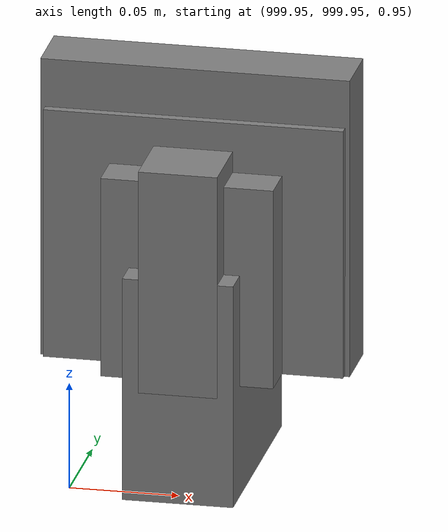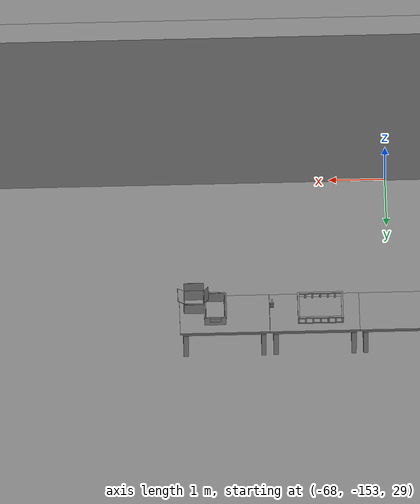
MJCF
<mujoco>
    <option gravity="0.000000000 0.000000000 -9.810000420" timestep="0.0049999999" integrator="implicitfast" density="1.225" viscosity="1.8000001e-05" noslip_iterations="10" iterations="100" sdf_iterations="50">
        <flag multiccd="disable"/>
    </option>
    <size memory="1000M"/>
    <compiler coordinate="local"/>
    <worldbody>
        <light cutoff="30" pos="0 1 1" dir="0 -1 -2"/>
        <light cutoff="30" pos="0 -1 1" dir="0 1 -2"/>
        <body pos="1000.000000000 1000.000000000 1.000000000" euler="0.000011953 0.000005123 -179.999984741" name="openloong_gripper_2f85_fix_base_usda_intel_box">
            <geom contype="1" conaffinity="1" density="1000" type="box" material="" rgba="0.500000000 0.500000000 0.500000000 1.000000000" solimp="0.899999976 0.949999988 0.001000000" friction="1.000000000 0.005000000 0.000100000" solref="0.020000000 1.000000000" margin="0" condim="3" group="0" pos="0.000000000 -0.000067139 0.000082284" quat="0.707106709 0.000000225 0.000000253 0.707106650" size="0.052800003 0.025300000 0.052800003" name="openloong_gripper_2f85_fix_base_usda_geom_FCBDBEA7_FFE3_49C6_9F52_89108464222C"/>
            <freejoint name="openloong_gripper_2f85_fix_base_usda_intel_box_joint"/>
            <site size="0.005000000 0.005000000 0.005000000" rgba="0.500000000 0.500000000 0.500000000 1.000000000" pos="0.000000000 0.000000000 0.000000000" quat="0.999961913 0.008726500 0.000000000 0.000000000" group="0" type="sphere" name="openloong_gripper_2f85_fix_base_usda_intel_boxsite"/>
        </body>
        <body pos="1000.000000000 999.999938965 1.000000000" euler="0.000000000 0.000000000 180.000000000" name="openloong_gripper_2f85_fix_base_usda_intelcore_i5">
            <geom contype="1" conaffinity="1" density="1000" type="box" material="" rgba="0.500000000 0.500000000 0.500000000 1.000000000" solimp="0.899999976 0.949999988 0.001000000" friction="1.000000000 0.005000000 0.000100000" solref="0.020000000 1.000000000" margin="0" condim="3" group="0" pos="0.000000000 0.000000000 0.051722717" quat="0.707106709 0.000000000 0.000000000 -0.707106769" size="0.052800000 0.018080002 0.052800000" name="openloong_gripper_2f85_fix_base_usda_geom_BCCCB434_B437_4029_AC8D_9703CF9488B4"/>
            <freejoint name="openloong_gripper_2f85_fix_base_usda_intelcore_i5_joint"/>
            <site size="0.005000000 0.005000000 0.005000000" rgba="0.500000000 0.500000000 0.500000000 1.000000000" pos="0.000000000 0.000000000 0.000000000" quat="0.999961913 0.008726534 0.000000000 0.000000000" group="0" type="sphere" name="openloong_gripper_2f85_fix_base_usda_intelcore_i5site"/>
        </body>
        <body pos="-66.005027771 -149.768493652 31.171264648" euler="160.226028442 -70.343513489 -176.699813843" mocap="true" name="spotlight5_SpotLight"/>
        <body pos="-66.360572815 -149.628311157 31.167764664" euler="-173.206497192 82.990631104 -173.107055664" mocap="true" name="spotlight6_SpotLight"/>
        <body pos="1000.000000000 1000.000000000 1.000000000" euler="0.000000000 0.000000000 180.000000000" name="openloong_gripper_2f85_fix_base_usda_wifi_box">
            <geom contype="1" conaffinity="1" density="1000" type="box" material="" rgba="0.500000000 0.500000000 0.500000000 1.000000000" solimp="0.899999976 0.949999988 0.001000000" friction="1.000000000 0.005000000 0.000100000" solref="0.020000000 1.000000000" margin="0" condim="3" group="0" pos="0.000000000 0.000000000 0.058978677" quat="0.000000000 0.000000047 0.000000000 1.000000000" size="0.068499997 0.018999999 0.059000000" name="openloong_gripper_2f85_fix_base_usda_geom_CA61DD2F_25D5_45C3_B92F_5000E40BD1D1"/>
            <freejoint name="openloong_gripper_2f85_fix_base_usda_wifi_box_joint"/>
            <site size="0.005000000 0.005000000 0.005000000" rgba="0.500000000 0.500000000 0.500000000 1.000000000" pos="0.000000000 0.000000000 0.000000000" quat="0.999961913 0.008726500 0.000000000 0.000000000" group="0" type="sphere" name="openloong_gripper_2f85_fix_base_usda_wifi_boxsite"/>
        </body>
        <body pos="1000.000000000 1000.000000000 1.000000000" euler="0.000000000 0.000000000 180.000000000" name="openloong_gripper_2f85_fix_base_usda_cpu_fan">
            <geom contype="1" conaffinity="1" density="1000" type="box" material="" rgba="0.500000000 0.500000000 0.500000000 1.000000000" solimp="0.899999976 0.949999988 0.001000000" friction="1.000000000 0.005000000 0.000100000" solref="0.020000000 1.000000000" margin="0" condim="3" group="0" pos="0.000000000 0.000000000 0.070034981" quat="0.000000000 0.000000000 0.000000000 1.000000000" size="0.070700005 0.014699999 0.070700005" name="openloong_gripper_2f85_fix_base_usda_geom_E3F388F2_4A1F_4000_9D7A_EF58941BE844"/>
            <freejoint name="openloong_gripper_2f85_fix_base_usda_cpu_fan_joint"/>
            <site size="0.005000000 0.005000000 0.005000000" rgba="0.500000000 0.500000000 0.500000000 1.000000000" pos="0.000000000 0.000000000 0.000000000" quat="0.999961913 0.008726535 0.000000000 0.000000000" group="0" type="sphere" name="openloong_gripper_2f85_fix_base_usda_cpu_fancsite"/>
        </body>
        <body pos="-65.888198853 -149.799346924 31.171499252" euler="-107.740707397 -33.283966064 76.697357178" mocap="true" name="spotlight3_SpotLight"/>
        <body pos="1000.000000000 1000.000000000 1.000000000" euler="0.000000000 0.000000000 180.000000000" name="openloong_gripper_2f85_fix_base_usda_battery_01">
            <geom contype="1" conaffinity="1" density="1000" type="box" material="" rgba="0.500000000 0.500000000 0.500000000 1.000000000" solimp="0.899999976 0.949999988 0.001000000" friction="1.000000000 0.005000000 0.000100000" solref="0.020000000 1.000000000" margin="0" condim="3" group="0" pos="-0.011123657 -0.041940309 0.101691343" quat="1.000000000 0.000000000 0.000000000 0.000000000" size="0.010800000 0.003375000 0.004725000" name="openloong_gripper_2f85_fix_base_usda_geom_D9E7F78D_7C33_432E_8BDD_4C954EC26A77"/>
            <geom contype="1" conaffinity="1" density="1000" type="box" material="" rgba="0.500000000 0.500000000 0.500000000 1.000000000" solimp="0.899999976 0.949999988 0.001000000" friction="1.000000000 0.005000000 0.000100000" solref="0.020000000 1.000000000" margin="0" condim="3" group="0" pos="-0.010876465 -0.044247437 0.047066893" quat="0.998702705 -0.050920475 0.000000000 0.000000000" size="0.009450001 0.002700000 0.024975000" name="openloong_gripper_2f85_fix_base_usda_geom_8815689E_2B96_46C6_894E_3B05D87EB9F1"/>
            <geom contype="1" conaffinity="1" density="1000" type="box" material="" rgba="0.500000000 0.500000000 0.500000000 1.000000000" solimp="0.899999976 0.949999988 0.001000000" friction="1.000000000 0.005000000 0.000100000" solref="0.020000000 1.000000000" margin="0" condim="3" group="0" pos="-0.001235962 -0.000659180 0.047381196" quat="1.000000000 0.000000000 0.000000000 0.000000000" size="0.039420001 0.039150000 0.047250003" name="openloong_gripper_2f85_fix_base_usda_geom_19D9F129_815C_4E70_A973_94E51340F044"/>
            <geom contype="1" conaffinity="1" density="1000" type="box" material="" rgba="0.500000000 0.500000000 0.500000000 1.000000000" solimp="0.899999976 0.949999988 0.001000000" friction="1.000000000 0.005000000 0.000100000" solref="0.020000000 1.000000000" margin="0" condim="3" group="0" pos="-0.010876465 -0.039138794 0.009851727" quat="1.000000000 0.000000000 0.000000000 0.000000000" size="0.009450001 0.010800000 0.013500000" name="openloong_gripper_2f85_fix_base_usda_geom_5CC1B9B1_C5BD_4FF8_B424_7BB6FA3D0E09"/>
            <geom contype="1" conaffinity="1" density="1000" type="box" material="" rgba="0.500000000 0.500000000 0.500000000 1.000000000" solimp="0.899999976 0.949999988 0.001000000" friction="1.000000000 0.005000000 0.000100000" solref="0.020000000 1.000000000" margin="0" condim="3" group="0" pos="-0.010876465 -0.041528322 0.071508206" quat="1.000000000 0.000000000 0.000000000 0.000000000" size="0.009450001 0.002700000 0.027000001" name="openloong_gripper_2f85_fix_base_usda_geom_3039782F_AFCE_42D6_BDC4_063E17A888EF"/>
            <freejoint name="openloong_gripper_2f85_fix_base_usda_battery_01_joint"/>
            <site size="0.005000000 0.005000000 0.005000000" rgba="0.500000000 0.500000000 0.500000000 1.000000000" pos="0.000000000 0.000000000 0.000000000" quat="0.999961913 0.008726500 0.000000000 0.000000000" group="0" type="sphere" name="openloong_gripper_2f85_fix_base_usda_battery_01site"/>
        </body>
        <body pos="-64.866622925 -149.383972168 30.183746338" euler="89.999984741 89.999946594 0.000000000" name="openloong_gripper_2f85_fix_base_usda_bluebox_01">
            <geom contype="1" conaffinity="1" density="1000" type="box" material="" rgba="0.500000000 0.500000000 0.500000000 1.000000000" solimp="0.899999976 0.949999988 0.001000000" friction="1.000000000 0.005000000 0.000100000" solref="0.020000000 1.000000000" margin="0" condim="3" group="0" pos="0.276580811 0.187225342 0.000068665" quat="0.707106948 0.000077471 0.707106352 0.000077486" size="0.100000001 0.057999998 0.010000000" name="openloong_gripper_2f85_fix_base_usda_geom_A4B4F0E7_09DC_470F_AAE0_BDD589C66AF4"/>
            <geom contype="1" conaffinity="1" density="1000" type="box" material="" rgba="0.500000000 0.500000000 0.500000000 1.000000000" solimp="0.899999976 0.949999988 0.001000000" friction="1.000000000 0.005000000 0.000100000" solref="0.020000000 1.000000000" margin="0" condim="3" group="0" pos="0.000000000 0.002883911 0.000000000" quat="0.999999881 0.000000000 0.000000000 0.000000000" size="0.254000008 0.003000000 0.172000006" name="openloong_gripper_2f85_fix_base_usda_geom_60293AA3_4CE9_4DC6_95F3_FE66047DEFFF"/>
            <geom contype="1" conaffinity="1" density="1000" type="box" material="" rgba="0.500000000 0.500000000 0.500000000 1.000000000" solimp="0.899999976 0.949999988 0.001000000" friction="1.000000000 0.005000000 0.000100000" solref="0.020000000 1.000000000" margin="0" condim="3" group="0" pos="0.000000000 0.124874115 0.173484802" quat="0.999796331 0.020176515 -0.000000015 0.000000030" size="0.259999990 0.119999997 0.007000000" name="openloong_gripper_2f85_fix_base_usda_geom_198D8D3B_8099_4773_A20E_1E13915B4295"/>
            <geom contype="1" conaffinity="1" density="1000" type="box" material="" rgba="0.500000000 0.500000000 0.500000000 1.000000000" solimp="0.899999976 0.949999988 0.001000000" friction="1.000000000 0.005000000 0.000100000" solref="0.020000000 1.000000000" margin="0" condim="3" group="0" pos="0.000000000 0.124874115 -0.173469543" quat="0.999796331 -0.020176545 -0.000000015 0.000000000" size="0.259999990 0.119999997 0.007000000" name="openloong_gripper_2f85_fix_base_usda_geom_518E7CF4_F630_4F79_9A7D_AB6E168BB1F1"/>
            <geom contype="1" conaffinity="1" density="1000" type="box" material="" rgba="0.500000000 0.500000000 0.500000000 1.000000000" solimp="0.899999976 0.949999988 0.001000000" friction="1.000000000 0.005000000 0.000100000" solref="0.020000000 1.000000000" margin="0" condim="3" group="0" pos="0.000000000 0.214008331 0.188980103" quat="0.999912977 0.013176724 0.000000015 0.000000000" size="0.259999990 0.029999999 0.012500000" name="openloong_gripper_2f85_fix_base_usda_geom_0E399F80_2989_4673_BDBE_42643B0CD1AB"/>
            <geom contype="1" conaffinity="1" density="1000" type="box" material="" rgba="0.500000000 0.500000000 0.500000000 1.000000000" solimp="0.899999976 0.949999988 0.001000000" friction="1.000000000 0.005000000 0.000100000" solref="0.020000000 1.000000000" margin="0" condim="3" group="0" pos="-0.258361816 0.125289917 0.001876831" quat="0.702796936 -0.020792112 0.710783124 0.020769298" size="0.189999998 0.119999997 0.009000000" name="openloong_gripper_2f85_fix_base_usda_geom_D994AE83_1668_498A_B732_4B8E26E01C91"/>
            <geom contype="1" conaffinity="1" density="1000" type="box" material="" rgba="0.500000000 0.500000000 0.500000000 1.000000000" solimp="0.899999976 0.949999988 0.001000000" friction="1.000000000 0.005000000 0.000100000" solref="0.020000000 1.000000000" margin="0" condim="3" group="0" pos="0.000000000 0.214008331 -0.188980103" quat="0.999912977 -0.013176769 0.000000030 0.000000015" size="0.259999990 0.029999999 0.012500000" name="openloong_gripper_2f85_fix_base_usda_geom_AF002BD9_7829_41B8_A394_3B8F270D3161"/>
            <geom contype="1" conaffinity="1" density="1000" type="box" material="" rgba="0.500000000 0.500000000 0.500000000 1.000000000" solimp="0.899999976 0.949999988 0.001000000" friction="1.000000000 0.005000000 0.000100000" solref="0.020000000 1.000000000" margin="0" condim="3" group="0" pos="-0.276611328 0.187225342 0.000068665" quat="0.707106650 0.000077441 0.707106709 0.000077456" size="0.100000001 0.057999998 0.010000000" name="openloong_gripper_2f85_fix_base_usda_geom_CF036560_1EF2_4020_8C59_2731B0489311"/>
            <geom contype="1" conaffinity="1" density="1000" type="box" material="" rgba="0.500000000 0.500000000 0.500000000 1.000000000" solimp="0.899999976 0.949999988 0.001000000" friction="1.000000000 0.005000000 0.000100000" solref="0.020000000 1.000000000" margin="0" condim="3" group="0" pos="0.258331299 0.125289917 0.001876831" quat="0.702851415 0.018856421 0.710823774 -0.019329369" size="0.189999998 0.119999997 0.009000000" name="openloong_gripper_2f85_fix_base_usda_geom_7E1D04BA_7A68_407C_9E10_377366537A99"/>
            <freejoint name="openloong_gripper_2f85_fix_base_usda_bluebox_01_joint"/>
            <site size="0.005000000 0.005000000 0.005000000" rgba="0.500000000 0.500000000 0.500000000 1.000000000" pos="0.000000000 0.000000000 0.000000000" quat="0.999961913 0.008726534 0.000000000 0.000000000" group="0" type="sphere" name="openloong_gripper_2f85_fix_base_usda_bluebox_01site"/>
        </body>
        <body pos="-64.496299744 -149.491867065 30.235729218" euler="0.000000000 0.000000000 89.999946594" name="openloong_gripper_2f85_fix_base_usda_cardboardbox_01">
            <geom contype="1" conaffinity="1" density="1000" type="box" material="" rgba="0.500000000 0.500000000 0.500000000 1.000000000" solimp="0.899999976 0.949999988 0.001000000" friction="1.000000000 0.005000000 0.000100000" solref="0.020000000 1.000000000" margin="0" condim="3" group="0" pos="-0.003166199 -0.004086494 0.005052090" quat="1.000000000 0.000000000 0.000000000 0.000000000" size="0.142499998 0.177500010 0.005000000" name="openloong_gripper_2f85_fix_base_usda_geom_0B710020_9B0B_4087_BB5F_90F0FE3D2568"/>
            <geom contype="1" conaffinity="1" density="1000" type="box" material="" rgba="0.500000000 0.500000000 0.500000000 1.000000000" solimp="0.899999976 0.949999988 0.001000000" friction="1.000000000 0.005000000 0.000100000" solref="0.020000000 1.000000000" margin="0" condim="3" group="0" pos="-0.003166199 0.170316696 0.150570869" quat="1.000000000 0.000000000 0.000000000 0.000000000" size="0.142499998 0.005000000 0.149999991" name="openloong_gripper_2f85_fix_base_usda_geom_ADDCF846_B0E1_4627_B7DD_3D8603F20EF1"/>
            <geom contype="1" conaffinity="1" density="1000" type="box" material="" rgba="0.500000000 0.500000000 0.500000000 1.000000000" solimp="0.899999976 0.949999988 0.001000000" friction="1.000000000 0.005000000 0.000100000" solref="0.020000000 1.000000000" margin="0" condim="3" group="0" pos="-0.147399902 -0.005307198 0.150570869" quat="1.000000000 0.000000000 0.000000000 0.000000000" size="0.005000000 0.177500010 0.149999991" name="openloong_gripper_2f85_fix_base_usda_geom_0353A363_D529_48E7_8127_38ED82FE25D8"/>
            <geom contype="1" conaffinity="1" density="1000" type="box" material="" rgba="0.500000000 0.500000000 0.500000000 1.000000000" solimp="0.899999976 0.949999988 0.001000000" friction="1.000000000 0.005000000 0.000100000" solref="0.020000000 1.000000000" margin="0" condim="3" group="0" pos="0.140275955 -0.005307198 0.150570869" quat="1.000000000 0.000000000 0.000000000 0.000000000" size="0.005000000 0.177500010 0.149999991" name="openloong_gripper_2f85_fix_base_usda_geom_EEBA0479_11C6_4A6A_BD47_97BC1BF8F420"/>
            <geom contype="1" conaffinity="1" density="1000" type="box" material="" rgba="0.500000000 0.500000000 0.500000000 1.000000000" solimp="0.899999976 0.949999988 0.001000000" friction="1.000000000 0.005000000 0.000100000" solref="0.020000000 1.000000000" margin="0" condim="3" group="0" pos="-0.003166199 -0.181550980 0.150570869" quat="1.000000000 0.000000000 0.000000000 0.000000000" size="0.142499998 0.005000000 0.149999991" name="openloong_gripper_2f85_fix_base_usda_geom_61C68898_6E8E_49A1_96CC_3B7D1DD386FE"/>
            <freejoint name="openloong_gripper_2f85_fix_base_usda_cardboardbox_01_joint"/>
            <site size="0.005000000 0.005000000 0.005000000" rgba="0.500000000 0.500000000 0.500000000 1.000000000" pos="0.000000000 0.000000000 0.000000000" quat="0.999961913 0.008726535 0.000000000 0.000000000" group="0" type="sphere" name="openloong_gripper_2f85_fix_base_usda_site_9D3A3DCF_5BFA_4071_B3B4_0EA27562B869"/>
            <body pos="0.139160156 -0.004048347 0.301930904" euler="-179.999954224 49.383502960 179.999954224" name="openloong_gripper_2f85_fix_base_usda_A1_006">
                <geom contype="1" conaffinity="1" density="1000" type="box" material="" rgba="0.500000000 0.500000000 0.500000000 1.000000000" solimp="0.899999976 0.949999988 0.001000000" friction="1.000000000 0.005000000 0.000100000" solref="0.020000000 1.000000000" margin="0" condim="3" group="0" pos="-0.071587563 0.000009537 0.001745224" quat="0.999999881 0.000000000 0.000000000 0.000000000" size="0.071249999 0.179999992 0.002500000" name="openloong_gripper_2f85_fix_base_usda_geom_9DEE6156_9C26_4D33_B8DF_CF4D0F7FE14A"/>
                <joint armature="0" stiffness="0.07" damping="0.0099999998" axis="0.000000 1.000000 0.000000" type="hinge" name="openloong_gripper_2f85_fix_base_usda_A1_006"/>
            </body>
            <body pos="-0.145902634 -0.004086494 0.301938057" euler="-180.000000000 -60.000011444 -180.000000000" name="openloong_gripper_2f85_fix_base_usda_A2_006">
                <geom contype="1" conaffinity="1" density="1000" type="box" material="" rgba="0.500000000 0.500000000 0.500000000 1.000000000" solimp="0.899999976 0.949999988 0.001000000" friction="1.000000000 0.005000000 0.000100000" solref="0.020000000 1.000000000" margin="0" condim="3" group="0" pos="0.071268082 0.000009537 0.002717972" quat="0.000002921 0.000000000 -0.000000030 0.999999881" size="0.071249999 0.179999992 0.002500000" name="openloong_gripper_2f85_fix_base_usda_geom_808331B5_697D_474C_A98E_CE3390B45FCA"/>
                <joint armature="0" stiffness="0.07" damping="0.0099999998" axis="0.000000 1.000000 0.000000" type="hinge" name="openloong_gripper_2f85_fix_base_usda_A2_006"/>
            </body>
            <body pos="-0.003385544 0.175991058 0.301930904" euler="-125.858116150 -0.000004561 0.000002331" name="openloong_gripper_2f85_fix_base_usda_B2_006">
                <geom contype="1" conaffinity="1" density="1000" type="box" material="" rgba="0.500000000 0.500000000 0.500000000 1.000000000" solimp="0.899999976 0.949999988 0.001000000" friction="1.000000000 0.005000000 0.000100000" solref="0.020000000 1.000000000" margin="0" condim="3" group="0" pos="0.000009537 -0.070939064 -0.002470016" quat="0.999614120 0.027776197 -0.000000015 0.000000030" size="0.137500003 0.064999998 0.005000000" name="openloong_gripper_2f85_fix_base_usda_geom_B7A1A5D1_057D_4DCB_9E77_E125B19DF19C"/>
                <joint armature="0" stiffness="0.07" damping="0.0099999998" axis="1.000000 0.000000 0.000000" type="hinge" name="openloong_gripper_2f85_fix_base_usda_B2_006"/>
            </body>
            <body pos="-0.003385544 -0.184140205 0.301938057" euler="147.805557251 0.000000000 0.000000000" name="openloong_gripper_2f85_fix_base_usda_B1_006">
                <geom contype="1" conaffinity="1" density="1000" type="box" material="" rgba="0.500000000 0.500000000 0.500000000 1.000000000" solimp="0.899999976 0.949999988 0.001000000" friction="1.000000000 0.005000000 0.000100000" solref="0.020000000 1.000000000" margin="0" condim="3" group="0" pos="-0.000028610 0.070202351 -0.002703667" quat="0.999614179 -0.027776167 0.000000000 0.000000000" size="0.137500003 0.064999998 0.005000000" name="openloong_gripper_2f85_fix_base_usda_geom_4DC63C0A_9A02_4016_B348_FCBE4933347A"/>
                <joint armature="0" stiffness="0.07" damping="0.0099999998" axis="1.000000 0.000000 0.000000" type="hinge" name="openloong_gripper_2f85_fix_base_usda_B1_006"/>
            </body>
        </body>
        <body pos="-65.882858276 -149.481979370 30.229999542" euler="-64.487716675 0.000000000 0.000000000" name="openloong_gripper_2f85_fix_base_usda_Barcode">
            <geom contype="1" conaffinity="1" density="1000" type="box" material="" rgba="0.500000000 0.500000000 0.500000000 1.000000000" solimp="0.899999976 0.949999988 0.001000000" friction="1.000000000 0.005000000 0.000100000" solref="0.020000000 1.000000000" margin="0" condim="3" group="0" pos="0.000000000 0.013038635 0.001419067" quat="0.000000000 0.000000000 0.000000000 1.000000119" size="0.034000002 0.010000000 0.017999999" name="openloong_gripper_2f85_fix_base_usda_geom_30E42E33_C107_45CB_B1B5_CBFE7EB734EE"/>
            <geom contype="1" conaffinity="1" density="1000" type="box" material="" rgba="0.500000000 0.500000000 0.500000000 1.000000000" solimp="0.899999976 0.949999988 0.001000000" friction="1.000000000 0.005000000 0.000100000" solref="0.020000000 1.000000000" margin="0" condim="3" group="0" pos="0.000000000 -0.035301208 -0.007095337" quat="0.000000000 0.000000000 -0.043619365 0.999048233" size="0.028999999 0.010000000 0.020000000" name="openloong_gripper_2f85_fix_base_usda_geom_EE7473FF_279F_4620_9FB7_54CAD85AA472"/>
            <geom contype="1" conaffinity="1" density="1000" type="box" material="" rgba="0.500000000 0.500000000 0.500000000 1.000000000" solimp="0.899999976 0.949999988 0.001000000" friction="1.000000000 0.005000000 0.000100000" solref="0.020000000 1.000000000" margin="0" condim="3" group="0" pos="0.000000000 -0.043411255 -0.011749268" quat="0.922262907 0.386563420 0.000000000 0.000000000" size="0.026000001 0.010000000 0.020000000" name="openloong_gripper_2f85_fix_base_usda_geom_5593D930_A471_471F_9BAA_35172C061CFE"/>
            <geom contype="1" conaffinity="1" density="1000" type="box" material="" rgba="0.500000000 0.500000000 0.500000000 1.000000000" solimp="0.899999976 0.949999988 0.001000000" friction="1.000000000 0.005000000 0.000100000" solref="0.020000000 1.000000000" margin="0" condim="3" group="0" pos="0.000000000 -0.016967773 -0.031860352" quat="0.000000000 0.000000000 0.000000000 1.000000119" size="0.008000000 0.010000000 0.013000000" name="openloong_gripper_2f85_fix_base_usda_geom_23DE49E8_7762_488C_A2EF_A250FA29E32B"/>
            <geom contype="1" conaffinity="1" density="1000" type="box" material="" rgba="0.500000000 0.500000000 0.500000000 1.000000000" solimp="0.899999976 0.949999988 0.001000000" friction="1.000000000 0.005000000 0.000100000" solref="0.020000000 1.000000000" margin="0" condim="3" group="0" pos="0.000000000 -0.001869202 0.000312805" quat="0.953716993 0.300705761 0.000000000 0.000000000" size="0.032000002 0.010000000 0.018999999" name="openloong_gripper_2f85_fix_base_usda_geom_7CA18A53_CD17_4823_88E7_7EF1CDF0E8E6"/>
            <geom contype="1" conaffinity="1" density="1000" type="box" material="" rgba="0.500000000 0.500000000 0.500000000 1.000000000" solimp="0.899999976 0.949999988 0.001000000" friction="1.000000000 0.005000000 0.000100000" solref="0.020000000 1.000000000" margin="0" condim="3" group="0" pos="0.000000000 -0.019531250 -0.003173828" quat="0.953716993 0.300705761 0.000000000 0.000000000" size="0.030999999 0.010000000 0.020000000" name="openloong_gripper_2f85_fix_base_usda_geom_850B9536_D519_4965_81A9_A80FFCBB9F3B"/>
            <geom contype="1" conaffinity="1" density="1000" type="box" material="" rgba="0.500000000 0.500000000 0.500000000 1.000000000" solimp="0.899999976 0.949999988 0.001000000" friction="1.000000000 0.005000000 0.000100000" solref="0.020000000 1.000000000" margin="0" condim="3" group="0" pos="0.000000000 -0.035301208 -0.007095337" quat="0.953716993 0.300705761 0.000000000 0.000000000" size="0.028999999 0.010000000 0.020000000" name="openloong_gripper_2f85_fix_base_usda_geom_CFD3A63E_2B21_4F4E_861A_CD1846FE227C"/>
            <geom contype="1" conaffinity="1" density="1000" type="box" material="" rgba="0.500000000 0.500000000 0.500000000 1.000000000" solimp="0.899999976 0.949999988 0.001000000" friction="1.000000000 0.005000000 0.000100000" solref="0.020000000 1.000000000" margin="0" condim="3" group="0" pos="0.000000000 -0.042617798 -0.071121216" quat="0.000000000 0.000000000 0.000000000 1.000000119" size="0.013000000 0.021000000 0.059999999" name="openloong_gripper_2f85_fix_base_usda_geom_0588F136_F49B_47E5_AB65_A6FEF782AAEE"/>
            <freejoint name="openloong_gripper_2f85_fix_base_usda_Barcode_joint"/>
            <site size="0.005000000 0.005000000 0.005000000" rgba="0.500000000 0.500000000 0.500000000 1.000000000" pos="0.000000000 0.000000000 0.000000000" quat="1.000000000 0.000000000 0.000000000 0.000000000" group="0" type="sphere" name="openloong_gripper_2f85_fix_base_usda_Barcode_site"/>
        </body>
        <body pos="-66.745018005 -149.392349243 30.184000015" euler="0.000000000 0.000000000 89.999946594" name="[22332197566263]_Basket_01">
            <geom contype="1" conaffinity="1" density="1000" type="box" material="" rgba="0.500000000 0.500000000 0.500000000 1.000000000" solimp="0.899999976 0.949999988 0.001000000" friction="1.000000000 0.005000000 0.000100000" solref="0.020000000 1.000000000" margin="0" condim="3" group="0" pos="-0.052425385 0.389207840 0.089787483" quat="0.707107008 0.000000000 0.000000000 0.707106411" size="0.014249999 0.014249999 0.059999999" name="[22332197566263]_geom_A5E78A79_2156_42C1_88A9_C0314F724777"/>
            <geom contype="1" conaffinity="1" density="1000" type="box" material="" rgba="0.500000000 0.500000000 0.500000000 1.000000000" solimp="0.899999976 0.949999988 0.001000000" friction="1.000000000 0.005000000 0.000100000" solref="0.020000000 1.000000000" margin="0" condim="3" group="0" pos="0.264015198 -0.133043289 0.089787483" quat="0.707107008 0.000000000 0.000000000 0.707106411" size="0.014249999 0.014249999 0.059999999" name="[22332197566263]_geom_4E4A1A79_9258_4350_AA33_D31614BB2A3E"/>
            <geom contype="1" conaffinity="1" density="1000" type="box" material="" rgba="0.500000000 0.500000000 0.500000000 1.000000000" solimp="0.899999976 0.949999988 0.001000000" friction="1.000000000 0.005000000 0.000100000" solref="0.020000000 1.000000000" margin="0" condim="3" group="0" pos="-0.264015198 -0.265548706 0.089793205" quat="0.707107008 0.000000000 0.000000000 0.707106411" size="0.014249999 0.014249999 0.059999999" name="[22332197566263]_geom_5BFC5E58_9540_4674_9E6D_C62E372DF697"/>
            <geom contype="1" conaffinity="1" density="1000" type="box" material="" rgba="0.500000000 0.500000000 0.500000000 1.000000000" solimp="0.899999976 0.949999988 0.001000000" friction="1.000000000 0.005000000 0.000100000" solref="0.020000000 1.000000000" margin="0" condim="3" group="0" pos="-0.160263062 -0.389322281 0.089793205" quat="0.707107008 0.000000000 0.000000000 0.707106411" size="0.014249999 0.014249999 0.059999999" name="[22332197566263]_geom_154EF4F8_36A0_4705_85C6_441C7A7C3B69"/>
            <geom contype="1" conaffinity="1" density="1000" type="box" material="" rgba="0.500000000 0.500000000 0.500000000 1.000000000" solimp="0.899999976 0.949999988 0.001000000" friction="1.000000000 0.005000000 0.000100000" solref="0.020000000 1.000000000" margin="0" condim="3" group="0" pos="0.162265778 -0.389322281 0.089787483" quat="0.707107008 0.000000000 0.000000000 0.707106411" size="0.014249999 0.014249999 0.059999999" name="[22332197566263]_geom_D3314992_B70F_408B_8471_45A36FCC6035"/>
            <geom contype="1" conaffinity="1" density="1000" type="box" material="" rgba="0.500000000 0.500000000 0.500000000 1.000000000" solimp="0.899999976 0.949999988 0.001000000" friction="1.000000000 0.005000000 0.000100000" solref="0.020000000 1.000000000" margin="0" condim="3" group="0" pos="0.264015198 0.389207840 0.089787483" quat="0.707107008 0.000000000 0.000000000 0.707106411" size="0.014249999 0.014249999 0.059999999" name="[22332197566263]_geom_2ABD1155_F811_48D1_BAF7_8AD90DDE7794"/>
            <geom contype="1" conaffinity="1" density="1000" type="box" material="" rgba="0.500000000 0.500000000 0.500000000 1.000000000" solimp="0.899999976 0.949999988 0.001000000" friction="1.000000000 0.005000000 0.000100000" solref="0.020000000 1.000000000" margin="0" condim="3" group="0" pos="-0.264015198 -0.133043289 0.089793205" quat="0.707107008 0.000000000 0.000000000 0.707106411" size="0.014249999 0.014249999 0.059999999" name="[22332197566263]_geom_3E9E2E72_592C_4C6B_BF77_8D56F20F083D"/>
            <geom contype="1" conaffinity="1" density="1000" type="box" material="" rgba="0.500000000 0.500000000 0.500000000 1.000000000" solimp="0.899999976 0.949999988 0.001000000" friction="1.000000000 0.005000000 0.000100000" solref="0.020000000 1.000000000" margin="0" condim="3" group="0" pos="-0.264026642 0.269256592 0.089793205" quat="0.707107008 0.000000000 0.000000000 0.707106411" size="0.014249999 0.014249999 0.059999999" name="[22332197566263]_geom_9D4588E2_9965_4974_80DA_6A2EFED2D2E1"/>
            <geom contype="1" conaffinity="1" density="1000" type="box" material="" rgba="0.500000000 0.500000000 0.500000000 1.000000000" solimp="0.899999976 0.949999988 0.001000000" friction="1.000000000 0.005000000 0.000100000" solref="0.020000000 1.000000000" margin="0" condim="3" group="0" pos="0.054462433 0.389207840 0.089787483" quat="0.707107008 0.000000000 0.000000000 0.707106411" size="0.014249999 0.014249999 0.059999999" name="[22332197566263]_geom_0CF898B5_CDBE_4434_BF16_5B7159A9AB9F"/>
            <geom contype="1" conaffinity="1" density="1000" type="box" material="" rgba="0.500000000 0.500000000 0.500000000 1.000000000" solimp="0.899999976 0.949999988 0.001000000" friction="1.000000000 0.005000000 0.000100000" solref="0.020000000 1.000000000" margin="0" condim="3" group="0" pos="0.054462433 -0.389322281 0.089787483" quat="0.707107008 0.000000000 0.000000000 0.707106411" size="0.014249999 0.014249999 0.059999999" name="[22332197566263]_geom_E61794D2_56CE_4FE3_ADB2_8C4A36C4953A"/>
            <geom contype="1" conaffinity="1" density="1000" type="box" material="" rgba="0.500000000 0.500000000 0.500000000 1.000000000" solimp="0.899999976 0.949999988 0.001000000" friction="1.000000000 0.005000000 0.000100000" solref="0.020000000 1.000000000" margin="0" condim="3" group="0" pos="0.264015198 0.269256592 0.089793205" quat="0.707107008 0.000000000 0.000000000 0.707106411" size="0.014249999 0.014249999 0.059999999" name="[22332197566263]_geom_FCADE11F_397E_472A_BD72_627557683569"/>
            <geom contype="1" conaffinity="1" density="1000" type="box" material="" rgba="0.500000000 0.500000000 0.500000000 1.000000000" solimp="0.899999976 0.949999988 0.001000000" friction="1.000000000 0.005000000 0.000100000" solref="0.020000000 1.000000000" margin="0" condim="3" group="0" pos="0.264015198 -0.389322281 0.089787483" quat="0.707107008 0.000000000 0.000000000 0.707106411" size="0.014249999 0.014249999 0.059999999" name="[22332197566263]_geom_59B2A077_E4C6_4F14_8E7F_2D1A0FC1B0D8"/>
            <geom contype="1" conaffinity="1" density="1000" type="box" material="" rgba="0.500000000 0.500000000 0.500000000 1.000000000" solimp="0.899999976 0.949999988 0.001000000" friction="1.000000000 0.005000000 0.000100000" solref="0.020000000 1.000000000" margin="0" condim="3" group="0" pos="0.000000000 0.000000000 0.015998840" quat="0.707107008 0.000000000 0.000000000 0.707106411" size="0.403499991 0.279000014 0.015750000" name="[22332197566263]_geom_C5AC36FC_98BB_47AF_9661_E7941CF0BB48"/>
            <geom contype="1" conaffinity="1" density="1000" type="box" material="" rgba="0.500000000 0.500000000 0.500000000 1.000000000" solimp="0.899999976 0.949999988 0.001000000" friction="1.000000000 0.005000000 0.000100000" solref="0.020000000 1.000000000" margin="0" condim="3" group="0" pos="0.000000000 -0.389476776 0.163619041" quat="0.707107008 0.000000000 0.000000000 0.707106411" size="0.015000000 0.277500004 0.015750000" name="[22332197566263]_geom_D3737BEA_B6D8_4741_98EB_BAD708EB60F4"/>
            <geom contype="1" conaffinity="1" density="1000" type="box" material="" rgba="0.500000000 0.500000000 0.500000000 1.000000000" solimp="0.899999976 0.949999988 0.001000000" friction="1.000000000 0.005000000 0.000100000" solref="0.020000000 1.000000000" margin="0" condim="3" group="0" pos="0.162265778 0.389207840 0.089787483" quat="0.707107008 0.000000000 0.000000000 0.707106411" size="0.014249999 0.014249999 0.059999999" name="[22332197566263]_geom_477B05A4_3AEF_4A26_8EDE_02E68CFA41B8"/>
            <geom contype="1" conaffinity="1" density="1000" type="box" material="" rgba="0.500000000 0.500000000 0.500000000 1.000000000" solimp="0.899999976 0.949999988 0.001000000" friction="1.000000000 0.005000000 0.000100000" solref="0.020000000 1.000000000" margin="0" condim="3" group="0" pos="0.000000000 0.389471054 0.163619041" quat="0.707107008 0.000000000 0.000000000 0.707106411" size="0.015000000 0.277500004 0.015750000" name="[22332197566263]_geom_25E629B2_EC88_40CD_8997_927A7D770D42"/>
            <geom contype="1" conaffinity="1" density="1000" type="box" material="" rgba="0.500000000 0.500000000 0.500000000 1.000000000" solimp="0.899999976 0.949999988 0.001000000" friction="1.000000000 0.005000000 0.000100000" solref="0.020000000 1.000000000" margin="0" condim="3" group="0" pos="-0.263511658 0.000000000 0.163619041" quat="0.707107008 0.000000000 0.000000000 0.707106411" size="0.403499991 0.015000000 0.015750000" name="[22332197566263]_geom_7EF69986_577E_48EE_A3DA_40A0267435F0"/>
            <geom contype="1" conaffinity="1" density="1000" type="box" material="" rgba="0.500000000 0.500000000 0.500000000 1.000000000" solimp="0.899999976 0.949999988 0.001000000" friction="1.000000000 0.005000000 0.000100000" solref="0.020000000 1.000000000" margin="0" condim="3" group="0" pos="-0.264015198 0.141334534 0.089793205" quat="0.707107008 0.000000000 0.000000000 0.707106411" size="0.014249999 0.014249999 0.059999999" name="[22332197566263]_geom_7E15A3C2_FB83_4CFE_AF07_2283E22320A4"/>
            <geom contype="1" conaffinity="1" density="1000" type="box" material="" rgba="0.500000000 0.500000000 0.500000000 1.000000000" solimp="0.899999976 0.949999988 0.001000000" friction="1.000000000 0.005000000 0.000100000" solref="0.020000000 1.000000000" margin="0" condim="3" group="0" pos="0.264015198 -0.265548706 0.089787483" quat="0.707107008 0.000000000 0.000000000 0.707106411" size="0.014249999 0.014249999 0.059999999" name="[22332197566263]_geom_EF96DD16_14E6_4F6C_AB42_51D8B6B67273"/>
            <geom contype="1" conaffinity="1" density="1000" type="box" material="" rgba="0.500000000 0.500000000 0.500000000 1.000000000" solimp="0.899999976 0.949999988 0.001000000" friction="1.000000000 0.005000000 0.000100000" solref="0.020000000 1.000000000" margin="0" condim="3" group="0" pos="-0.160263062 0.389207840 0.089787483" quat="0.707107008 0.000000000 0.000000000 0.707106411" size="0.014249999 0.014249999 0.059999999" name="[22332197566263]_geom_63C3970C_90FC_4A54_B02A_1F3CB7596614"/>
            <geom contype="1" conaffinity="1" density="1000" type="box" material="" rgba="0.500000000 0.500000000 0.500000000 1.000000000" solimp="0.899999976 0.949999988 0.001000000" friction="1.000000000 0.005000000 0.000100000" solref="0.020000000 1.000000000" margin="0" condim="3" group="0" pos="-0.052425385 -0.389322281 0.089787483" quat="0.707107008 0.000000000 0.000000000 0.707106411" size="0.014249999 0.014249999 0.059999999" name="[22332197566263]_geom_8F411489_6CA6_4E1D_B25B_BB0D24C62717"/>
            <geom contype="1" conaffinity="1" density="1000" type="box" material="" rgba="0.500000000 0.500000000 0.500000000 1.000000000" solimp="0.899999976 0.949999988 0.001000000" friction="1.000000000 0.005000000 0.000100000" solref="0.020000000 1.000000000" margin="0" condim="3" group="0" pos="-0.264026642 -0.389322281 0.089793205" quat="0.707107008 0.000000000 0.000000000 0.707106411" size="0.014249999 0.014249999 0.059999999" name="[22332197566263]_geom_06E326C0_8B9B_479A_A319_EDA7A142C12F"/>
            <geom contype="1" conaffinity="1" density="1000" type="box" material="" rgba="0.500000000 0.500000000 0.500000000 1.000000000" solimp="0.899999976 0.949999988 0.001000000" friction="1.000000000 0.005000000 0.000100000" solref="0.020000000 1.000000000" margin="0" condim="3" group="0" pos="0.264015198 0.141334534 0.089787483" quat="0.707107008 0.000000000 0.000000000 0.707106411" size="0.014249999 0.014249999 0.059999999" name="[22332197566263]_geom_5272F9BE_792D_4548_BF02_3D62D5123942"/>
            <geom contype="1" conaffinity="1" density="1000" type="box" material="" rgba="0.500000000 0.500000000 0.500000000 1.000000000" solimp="0.899999976 0.949999988 0.001000000" friction="1.000000000 0.005000000 0.000100000" solref="0.020000000 1.000000000" margin="0" condim="3" group="0" pos="-0.264015198 0.389207840 0.089793205" quat="0.707107008 0.000000000 0.000000000 0.707106411" size="0.014249999 0.014249999 0.059999999" name="[22332197566263]_geom_AE4DC905_D00C_40E3_800A_3AA6B236437A"/>
            <geom contype="1" conaffinity="1" density="1000" type="box" material="" rgba="0.500000000 0.500000000 0.500000000 1.000000000" solimp="0.899999976 0.949999988 0.001000000" friction="1.000000000 0.005000000 0.000100000" solref="0.020000000 1.000000000" margin="0" condim="3" group="0" pos="0.264015198 0.004480362 0.089787483" quat="0.707107008 0.000000000 0.000000000 0.707106411" size="0.014249999 0.014249999 0.059999999" name="[22332197566263]_geom_3681BA63_C51D_46D6_8C57_A319A044E27D"/>
            <geom contype="1" conaffinity="1" density="1000" type="box" material="" rgba="0.500000000 0.500000000 0.500000000 1.000000000" solimp="0.899999976 0.949999988 0.001000000" friction="1.000000000 0.005000000 0.000100000" solref="0.020000000 1.000000000" margin="0" condim="3" group="0" pos="0.263694763 -0.000011444 0.163619041" quat="0.707107008 0.000000000 0.000000000 0.707106411" size="0.403499991 0.015000000 0.015750000" name="[22332197566263]_geom_1656CE52_1700_4C2D_80AB_8B2A62F39034"/>
            <geom contype="1" conaffinity="1" density="1000" type="box" material="" rgba="0.500000000 0.500000000 0.500000000 1.000000000" solimp="0.899999976 0.949999988 0.001000000" friction="1.000000000 0.005000000 0.000100000" solref="0.020000000 1.000000000" margin="0" condim="3" group="0" pos="-0.264015198 0.004480362 0.089793205" quat="0.707107008 0.000000000 0.000000000 0.707106411" size="0.014249999 0.014249999 0.059999999" name="[22332197566263]_geom_EF39C5A7_13E3_40E9_967A_B48E0DB38B6A"/>
            <freejoint name="[22332197566263]_joint_43F905C0_2304_40E1_9F2A_0C9EE628FE82"/>
        </body>
        <body pos="0.000000000 0.000000000 0.000000000" euler="0.000000000 0.000000000 0.000000000" name="Static Objects_Static Objects">
            <geom contype="1" conaffinity="1" density="1000" type="box" material="" rgba="0.500000000 0.500000000 0.500000000 1.000000000" solimp="0.899999976 0.949999988 0.001000000" friction="1.000000000 0.005000000 0.000100000" solref="0.020000000 1.000000000" margin="0" condim="3" group="0" pos="-67.544113159 -149.365814209 29.727830887" quat="0.500000417 0.499999970 0.499999553 0.499999970" size="0.381000012 0.319999993 0.041000001" name="Static Objects_geom_57E09D96_4566_4FBD_BB8E_FD75583BAEC5"/>
            <geom contype="1" conaffinity="1" density="1000" type="box" material="" rgba="0.500000000 0.500000000 0.500000000 1.000000000" solimp="0.899999976 0.949999988 0.001000000" friction="1.000000000 0.005000000 0.000100000" solref="0.020000000 1.000000000" margin="0" condim="3" group="0" pos="-68.239501953 -149.365814209 30.086868286" quat="0.500000417 0.499999970 0.499999553 0.499999970" size="0.370999992 0.039500002 0.745000005" name="Static Objects_geom_0DAB7FE9_2A96_4B2B_B557_3EE085A584F6"/>
            <geom contype="1" conaffinity="1" density="1000" type="box" material="" rgba="0.500000000 0.500000000 0.500000000 1.000000000" solimp="0.899999976 0.949999988 0.001000000" friction="1.000000000 0.005000000 0.000100000" solref="0.020000000 1.000000000" margin="0" condim="3" group="0" pos="-68.239501953 -149.365814209 30.147235870" quat="0.500000417 0.499999970 0.499999553 0.499999970" size="0.400000006 0.022000000 0.800000012" name="Static Objects_geom_6317062A_865E_4FCD_81F9_4711B3CFADAD"/>
            <geom contype="1" conaffinity="1" density="1000" type="box" material="" rgba="0.500000000 0.500000000 0.500000000 1.000000000" solimp="0.899999976 0.949999988 0.001000000" friction="1.000000000 0.005000000 0.000100000" solref="0.020000000 1.000000000" margin="0" condim="3" group="0" pos="-68.934890747 -149.365814209 29.727830887" quat="0.500000417 0.499999970 0.499999553 0.499999970" size="0.381000012 0.319999993 0.041000001" name="Static Objects_geom_F572E094_2C71_4E40_BA60_59168230B2E2"/>
            <geom contype="1" conaffinity="1" density="1000" type="box" material="" rgba="0.500000000 0.500000000 0.500000000 1.000000000" solimp="0.899999976 0.949999988 0.001000000" friction="1.000000000 0.005000000 0.000100000" solref="0.020000000 1.000000000" margin="0" condim="3" group="0" pos="-68.239501953 -149.365814209 29.561563492" quat="0.500000417 0.499999970 0.499999553 0.499999970" size="0.020000000 0.022000000 0.660000026" name="Static Objects_geom_4D3990D2_0FDB_4EC6_AA41_4ECE156D1BF3"/>
            <geom contype="1" conaffinity="1" density="1000" type="box" material="" rgba="0.500000000 0.500000000 0.500000000 1.000000000" solimp="0.899999976 0.949999988 0.001000000" friction="1.000000000 0.005000000 0.000100000" solref="0.020000000 1.000000000" margin="0" condim="3" group="0" pos="-65.945671082 -149.365814209 29.727830887" quat="0.500000417 0.499999970 0.499999553 0.499999970" size="0.381000012 0.319999993 0.041000001" name="Static Objects_geom_C313B3D9_D4B0_4E3C_8675_E0E0EA0DE788"/>
            <geom contype="1" conaffinity="1" density="1000" type="box" material="" rgba="0.500000000 0.500000000 0.500000000 1.000000000" solimp="0.899999976 0.949999988 0.001000000" friction="1.000000000 0.005000000 0.000100000" solref="0.020000000 1.000000000" margin="0" condim="3" group="0" pos="-66.641059875 -149.365814209 30.086868286" quat="0.500000417 0.499999970 0.499999553 0.499999970" size="0.370999992 0.039500002 0.745000005" name="Static Objects_geom_EAB4ECBB_B01D_4C5D_94C7_D65CA313317F"/>
            <geom contype="1" conaffinity="1" density="1000" type="box" material="" rgba="0.500000000 0.500000000 0.500000000 1.000000000" solimp="0.899999976 0.949999988 0.001000000" friction="1.000000000 0.005000000 0.000100000" solref="0.020000000 1.000000000" margin="0" condim="3" group="0" pos="-66.641059875 -149.365814209 30.147235870" quat="0.500000417 0.499999970 0.499999553 0.499999970" size="0.400000006 0.022000000 0.800000012" name="Static Objects_geom_74AC276C_2C80_48EE_9F2F_F1100F540037"/>
            <geom contype="1" conaffinity="1" density="1000" type="box" material="" rgba="0.500000000 0.500000000 0.500000000 1.000000000" solimp="0.899999976 0.949999988 0.001000000" friction="1.000000000 0.005000000 0.000100000" solref="0.020000000 1.000000000" margin="0" condim="3" group="0" pos="-67.336448669 -149.365814209 29.727830887" quat="0.500000417 0.499999970 0.499999553 0.499999970" size="0.381000012 0.319999993 0.041000001" name="Static Objects_geom_2AF00B50_F909_47FE_860C_2F7E6394B975"/>
            <geom contype="1" conaffinity="1" density="1000" type="box" material="" rgba="0.500000000 0.500000000 0.500000000 1.000000000" solimp="0.899999976 0.949999988 0.001000000" friction="1.000000000 0.005000000 0.000100000" solref="0.020000000 1.000000000" margin="0" condim="3" group="0" pos="-66.641059875 -149.365814209 29.561563492" quat="0.500000417 0.499999970 0.499999553 0.499999970" size="0.020000000 0.022000000 0.660000026" name="Static Objects_geom_5E557576_967F_43EE_AC20_49D48BC1C738"/>
            <geom contype="1" conaffinity="1" density="1000" type="box" material="" rgba="0.500000000 0.500000000 0.500000000 1.000000000" solimp="0.899999976 0.949999988 0.001000000" friction="1.000000000 0.005000000 0.000100000" solref="0.020000000 1.000000000" margin="0" condim="3" group="0" pos="-64.338577271 -149.365814209 29.727830887" quat="0.500000417 0.499999970 0.499999553 0.499999970" size="0.381000012 0.319999993 0.041000001" name="Static Objects_geom_4345B1EB_4797_461F_ADDA_283ACE1CE74C"/>
            <geom contype="1" conaffinity="1" density="1000" type="box" material="" rgba="0.500000000 0.500000000 0.500000000 1.000000000" solimp="0.899999976 0.949999988 0.001000000" friction="1.000000000 0.005000000 0.000100000" solref="0.020000000 1.000000000" margin="0" condim="3" group="0" pos="-65.033966064 -149.365814209 30.086868286" quat="0.500000417 0.499999970 0.499999553 0.499999970" size="0.370999992 0.039500002 0.745000005" name="Static Objects_geom_605A9121_8C55_496E_8F3D_8C5F91520B62"/>
            <geom contype="1" conaffinity="1" density="1000" type="box" material="" rgba="0.500000000 0.500000000 0.500000000 1.000000000" solimp="0.899999976 0.949999988 0.001000000" friction="1.000000000 0.005000000 0.000100000" solref="0.020000000 1.000000000" margin="0" condim="3" group="0" pos="-65.033966064 -149.365814209 30.147235870" quat="0.500000417 0.499999970 0.499999553 0.499999970" size="0.400000006 0.022000000 0.800000012" name="Static Objects_geom_EBB2F1B5_B610_40D7_A996_D40EB70EF683"/>
            <geom contype="1" conaffinity="1" density="1000" type="box" material="" rgba="0.500000000 0.500000000 0.500000000 1.000000000" solimp="0.899999976 0.949999988 0.001000000" friction="1.000000000 0.005000000 0.000100000" solref="0.020000000 1.000000000" margin="0" condim="3" group="0" pos="-65.729354858 -149.365814209 29.727830887" quat="0.500000417 0.499999970 0.499999553 0.499999970" size="0.381000012 0.319999993 0.041000001" name="Static Objects_geom_302DA0C1_B67B_4D5B_BA27_87D904793599"/>
            <geom contype="1" conaffinity="1" density="1000" type="box" material="" rgba="0.500000000 0.500000000 0.500000000 1.000000000" solimp="0.899999976 0.949999988 0.001000000" friction="1.000000000 0.005000000 0.000100000" solref="0.020000000 1.000000000" margin="0" condim="3" group="0" pos="-65.033966064 -149.365814209 29.561563492" quat="0.500000417 0.499999970 0.499999553 0.499999970" size="0.020000000 0.022000000 0.660000026" name="Static Objects_geom_8328B318_EB7D_42FF_86B4_88A37F6F6CD8"/>
            <geom contype="1" conaffinity="1" density="1000" type="box" material="" rgba="0.500000000 0.500000000 0.500000000 1.000000000" solimp="0.899999976 0.949999988 0.001000000" friction="1.000000000 0.005000000 0.000100000" solref="0.020000000 1.000000000" margin="0" condim="3" group="0" pos="-61.754566193 -137.853729248 33.906845093" quat="0.707107067 0.000000000 0.000000000 0.707106471" size="0.759999990 0.759999990 4.500000000" name="Static Objects_geom_A4F6F257_8BD1_43AF_8A38_CF139EAB4208"/>
            <geom contype="1" conaffinity="1" density="1000" type="box" material="" rgba="0.500000000 0.500000000 0.500000000 1.000000000" solimp="0.899999976 0.949999988 0.001000000" friction="1.000000000 0.005000000 0.000100000" solref="0.020000000 1.000000000" margin="0" condim="3" group="0" pos="-57.511135101 -144.927108765 31.707921982" quat="1.000000000 0.000000000 0.000000000 0.000000000" size="0.200000003 8.000000000 2.299999952" name="Static Objects_geom_8C347015_9137_46E2_9CF5_6DC58ABE369E"/>
            <geom contype="1" conaffinity="1" density="1000" type="box" material="" rgba="0.500000000 0.500000000 0.500000000 1.000000000" solimp="0.899999976 0.949999988 0.001000000" friction="1.000000000 0.005000000 0.000100000" solref="0.020000000 1.000000000" margin="0" condim="3" group="0" pos="-80.517646790 -157.574050903 31.688196182" quat="0.707107067 0.000000000 0.000000000 0.707106471" size="0.600000024 0.600000024 2.299999952" name="Static Objects_geom_F34F271A_4C64_47B7_BF87_07016D257460"/>
            <geom contype="1" conaffinity="1" density="1000" type="box" material="" rgba="0.500000000 0.500000000 0.500000000 1.000000000" solimp="0.899999976 0.949999988 0.001000000" friction="1.000000000 0.005000000 0.000100000" solref="0.020000000 1.000000000" margin="0" condim="3" group="0" pos="-80.711044312 -147.414932251 31.666158676" quat="1.000000000 0.000000000 0.000000000 0.000000000" size="0.200000003 10.000000000 2.299999952" name="Static Objects_geom_11D45937_F36B_4BDD_BFEF_01792BDE9939"/>
            <geom contype="1" conaffinity="1" density="1000" type="box" material="" rgba="0.500000000 0.500000000 0.500000000 1.000000000" solimp="0.899999976 0.949999988 0.001000000" friction="1.000000000 0.005000000 0.000100000" solref="0.020000000 1.000000000" margin="0" condim="3" group="0" pos="-57.687217712 -137.434692383 31.688196182" quat="0.707107067 0.000000000 0.000000000 0.707106471" size="0.600000024 0.600000024 2.299999952" name="Static Objects_geom_3122F5DA_1889_4FB1_A5F8_AB8C4CCF0759"/>
            <geom contype="1" conaffinity="1" density="1000" type="box" material="" rgba="0.500000000 0.500000000 0.500000000 1.000000000" solimp="0.899999976 0.949999988 0.001000000" friction="1.000000000 0.005000000 0.000100000" solref="0.020000000 1.000000000" margin="0" condim="3" group="0" pos="-69.537033081 -140.263229370 31.714921951" quat="0.707107067 0.000000000 0.000000000 0.707106471" size="0.759999990 4.500000000 2.299999952" name="Static Objects_geom_7C4562BB_5331_4D87_9550_5C617268F310"/>
            <geom contype="1" conaffinity="1" density="1000" type="box" material="" rgba="0.500000000 0.500000000 0.500000000 1.000000000" solimp="0.899999976 0.949999988 0.001000000" friction="1.000000000 0.005000000 0.000100000" solref="0.020000000 1.000000000" margin="0" condim="3" group="0" pos="-80.073638916 -137.853713989 33.906845093" quat="0.707107067 0.000000000 0.000000000 0.707106471" size="0.759999990 0.759999990 4.500000000" name="Static Objects_geom_D83BA1E0_6E8B_4FBF_80AA_D7114F6E0A30"/>
            <geom contype="1" conaffinity="1" density="1000" type="box" material="" rgba="0.500000000 0.500000000 0.500000000 1.000000000" solimp="0.899999976 0.949999988 0.001000000" friction="1.000000000 0.005000000 0.000100000" solref="0.020000000 1.000000000" margin="0" condim="3" group="0" pos="-73.406707764 -155.734664917 31.707921982" quat="1.000000000 0.000000000 0.000000000 0.000000000" size="0.200000003 3.000000000 2.299999952" name="Static Objects_geom_253CC8B7_5D23_4D41_A818_A4919D80A377"/>
            <geom contype="1" conaffinity="1" density="1000" type="box" material="" rgba="0.500000000 0.500000000 0.500000000 1.000000000" solimp="0.899999976 0.949999988 0.001000000" friction="1.000000000 0.005000000 0.000100000" solref="0.020000000 1.000000000" margin="0" condim="3" group="0" pos="-68.497543335 -137.448257446 31.707921982" quat="0.707107067 0.000000000 0.000000000 0.707106471" size="0.200000003 14.000000000 2.299999952" name="Static Objects_geom_E90CFDA2_3C5D_4034_8481_BF1A1F6421F5"/>
            <geom contype="1" conaffinity="1" density="1000" type="cylinder" material="" rgba="0.500000000 0.500000000 0.500000000 1.000000000" solimp="0.899999976 0.949999988 0.001000000" friction="1.000000000 0.005000000 0.000100000" solref="0.020000000 1.000000000" margin="0" condim="3" group="0" pos="-68.868522644 -142.134506226 31.711090088" quat="0.707107067 0.000000000 0.000000000 0.707106471" size="0.509999990 2.299999952 1.000000000" name="Static Objects_geom_E2391717_DFA2_4D96_AC98_7B9A0EEDDFFE"/>
            <geom contype="1" conaffinity="1" density="1000" type="plane" material="" rgba="0.500000000 0.500000000 0.500000000 1.000000000" solimp="0.899999976 0.949999988 0.001000000" friction="1.000000000 0.005000000 0.000100000" solref="0.020000000 1.000000000" margin="0" condim="3" group="0" pos="-72.873703003 -147.131927490 29.409669876" quat="1.000000000 0.000000000 0.000000000 0.000000000" size="18.000000000 14.000000000 1.000000000" name="Static Objects_geom_0CEC28F2_3DCD_4641_BF5E_D6C7CF92F576"/>
            <geom contype="1" conaffinity="1" density="1000" type="box" material="" rgba="0.500000000 0.500000000 0.500000000 1.000000000" solimp="0.899999976 0.949999988 0.001000000" friction="1.000000000 0.005000000 0.000100000" solref="0.020000000 1.000000000" margin="0" condim="3" group="0" pos="-79.943580627 -157.782272339 31.707921982" quat="0.707107067 0.000000000 0.000000000 0.707106471" size="0.200000003 7.000000000 2.299999952" name="Static Objects_geom_AAB3F4DC_915D_4FC1_8B69_DF72B622B44A"/>
            <geom contype="1" conaffinity="1" density="1000" type="box" material="" rgba="0.500000000 0.500000000 0.500000000 1.000000000" solimp="0.899999976 0.949999988 0.001000000" friction="1.000000000 0.005000000 0.000100000" solref="0.020000000 1.000000000" margin="0" condim="3" group="0" pos="-65.421028137 -152.903442383 31.707921982" quat="0.707107067 0.000000000 0.000000000 0.707106471" size="0.200000003 7.800000191 2.299999952" name="Static Objects_geom_10F98BAC_0F42_413D_A789_EBE21E613C1F"/>
            <geom contype="1" conaffinity="1" density="1000" type="box" material="" rgba="0.500000000 0.500000000 0.500000000 1.000000000" solimp="0.899999976 0.949999988 0.001000000" friction="1.000000000 0.005000000 0.000100000" solref="0.020000000 1.000000000" margin="0" condim="3" group="0" pos="-74.776908875 -149.964416504 31.688196182" quat="1.000000000 0.000000000 0.000000000 0.000000000" size="0.600000024 0.409999996 2.299999952" name="Static Objects_geom_2E752B2F_398B_43B4_8434_B5BC16825615"/>
            <geom contype="1" conaffinity="1" density="1000" type="cylinder" material="" rgba="0.500000000 0.500000000 0.500000000 1.000000000" solimp="0.899999976 0.949999988 0.001000000" friction="1.000000000 0.005000000 0.000100000" solref="0.020000000 1.000000000" margin="0" condim="3" group="0" pos="-60.161884308 -142.134506226 31.711090088" quat="0.707107067 0.000000000 0.000000000 0.707106471" size="0.509999990 2.299999952 1.000000000" name="Static Objects_geom_CE312EA4_4AEE_444F_B96C_444B9CEB206B"/>
            <geom contype="1" conaffinity="1" density="1000" type="cylinder" material="" rgba="0.500000000 0.500000000 0.500000000 1.000000000" solimp="0.899999976 0.949999988 0.001000000" friction="1.000000000 0.005000000 0.000100000" solref="0.020000000 1.000000000" margin="0" condim="3" group="0" pos="-75.382453918 -149.963455200 31.711090088" quat="0.707107067 0.000000000 0.000000000 0.707106471" size="0.409999996 2.299999952 1.000000000" name="Static Objects_geom_603BB11F_AD6C_4236_A4CF_B6B0AC3095B9"/>
            <geom contype="1" conaffinity="1" density="1000" type="cylinder" material="" rgba="0.500000000 0.500000000 0.500000000 1.000000000" solimp="0.899999976 0.949999988 0.001000000" friction="1.000000000 0.005000000 0.000100000" solref="0.020000000 1.000000000" margin="0" condim="3" group="0" pos="-74.154960632 -149.963455200 31.711090088" quat="0.707107067 0.000000000 0.000000000 0.707106471" size="0.409999996 2.299999952 1.000000000" name="Static Objects_geom_9D36DB92_F5DE_4AAB_A761_BCF0E300875C"/>
            <geom contype="1" conaffinity="1" density="1000" type="cylinder" material="" rgba="0.500000000 0.500000000 0.500000000 1.000000000" solimp="0.899999976 0.949999988 0.001000000" friction="1.000000000 0.005000000 0.000100000" solref="0.020000000 1.000000000" margin="0" condim="3" group="0" pos="-77.566612244 -142.134506226 31.711090088" quat="0.707107067 0.000000000 0.000000000 0.707106471" size="0.509999990 2.299999952 1.000000000" name="Static Objects_geom_9433794E_5D4F_4BF4_9B07_83116772D335"/>
        </body>
        <body pos="-66.291030884 -149.869689941 29.018842697" euler="0.000000000 0.000000000 89.999946594" mocap="true" name="openloong_gripper_2f85_fix_base_usda_leftHandMocap"/>
        <body pos="-66.291030884 -149.869689941 29.018842697" euler="0.000000000 0.000000000 89.999946594" mocap="true" name="openloong_gripper_2f85_fix_base_usda_rightHandMocap"/>
        <body pos="-66.291030884 -149.869689941 30.218843460" euler="0.000000000 0.000000000 89.999946594" name="openloong_gripper_2f85_fix_base_usda_base_link">
            <geom contype="1" conaffinity="1" density="1000" type="mesh" material="" rgba="0.783999979 0.783999979 0.783999979 1.000000000" solimp="0.899999976 0.949999988 0.001000000" friction="1.000000000 0.005000000 0.000100000" solref="0.020000000 1.000000000" margin="0" condim="3" group="3" mesh="base_link" pos="0.000000000 0.000000000 0.000000000" quat="1.000000000 0.000000000 0.000000000 0.000000000" size="1.000000000 1.000000000 1.000000000" name="openloong_gripper_2f85_fix_base_usda__geom_7_048E0B91_2914_43E8_BF85_6EF8D7D95540"/>
            <site size="0.005000000 0.005000000 0.005000000" rgba="0.500000000 0.500000000 0.500000000 1.000000000" pos="0.000000000 0.000000000 0.000000000" quat="1.000000000 0.000000000 0.000000000 0.000000000" group="0" type="sphere" name="openloong_gripper_2f85_fix_base_usda_imu"/>
            <inertial mass="22.447001" pos="-0.005664100 -0.001336700 0.238289997" diaginertia="0.374352545 0.277180195 0.220617250" quat="0.999247074 0.035235517 -0.015086859 0.006023135"/>
            <body pos="0.000000000 0.000000000 0.299997330" euler="0.000000000 0.000000000 0.000000000" name="openloong_gripper_2f85_fix_base_usda_dummy_body">
                <geom contype="1" conaffinity="1" density="1000" type="sphere" material="" rgba="0.783999979 0.783999979 0.783999979 1.000000000" solimp="0.899999976 0.949999988 0.001000000" friction="1.000000000 0.005000000 0.000100000" solref="0.020000000 1.000000000" margin="0" condim="3" group="3" pos="0.000000000 0.000000000 0.000000000" quat="1.000000000 0.000000000 0.000000000 0.000000000" size="0.010000000 0.000000000 0.000000000" name="openloong_gripper_2f85_fix_base_usda__geom_8_604DB801_89EA_49DE_BC9B_D4B0F6D730B8"/>
                <joint armature="0.0099999998" stiffness="0" damping="0.1" axis="0.000000 0.000000 1.000000" type="hinge" name="openloong_gripper_2f85_fix_base_usda_dummy_joint"/>
                <site size="0.010000000 0.005000000 0.005000000" rgba="0.500000000 0.500000000 0.500000000 1.000000000" pos="0.000000000 0.000000000 0.000000000" quat="1.000000000 0.000000000 0.000000000 0.000000000" group="3" type="sphere" name="openloong_gripper_2f85_fix_base_usda_dummy_site"/>
            </body>
            <body pos="0.009002686 0.000000000 0.406400681" euler="0.000000000 0.000000000 0.000000000" name="openloong_gripper_2f85_fix_base_usda_Link_head_yaw">
                <geom contype="1" conaffinity="1" density="1000" type="mesh" material="" rgba="0.783999979 0.783999979 0.783999979 1.000000000" solimp="0.899999976 0.949999988 0.001000000" friction="1.000000000 0.005000000 0.000100000" solref="0.020000000 1.000000000" margin="0" condim="3" group="3" mesh="Link_head_yaw" pos="0.000000000 0.000000000 0.000000000" quat="1.000000000 0.000000000 0.000000000 0.000000000" size="1.000000000 1.000000000 1.000000000" name="openloong_gripper_2f85_fix_base_usda__geom_10_9CDB2020_AA53_427F_B534_588EE44DBC78"/>
                <inertial mass="0.84249002" pos="0.000000000 -0.002081400 0.044801001" diaginertia="0.000700588 0.000629000 0.000553812" quat="0.706933022 -0.015675601 0.015677100 0.706933022"/>
                <body pos="0.000000000 -0.034599304 0.048500061" euler="0.000000000 0.000000000 0.000000000" name="openloong_gripper_2f85_fix_base_usda_Link_head_pitch">
                    <geom contype="1" conaffinity="1" density="1000" type="mesh" material="" rgba="0.783999979 0.783999979 0.783999979 1.000000000" solimp="0.899999976 0.949999988 0.001000000" friction="1.000000000 0.005000000 0.000100000" solref="0.020000000 1.000000000" margin="0" condim="3" group="3" mesh="Link_head_pitch" pos="0.000000000 0.000000000 0.000000000" quat="1.000000000 0.000000000 0.000000000 0.000000000" size="1.000000000 1.000000000 1.000000000" name="openloong_gripper_2f85_fix_base_usda__geom_12_EC231E73_F69B_474F_B75F_089E1587CA01"/>
                    <inertial mass="1.3943" pos="0.020569000 0.033004001 0.125000000" diaginertia="0.006381400 0.006289940 0.004481460" quat="0.973390222 0.008406822 0.228157058 0.019624906"/>
                    <body pos="0.000000000 0.029998779 0.000000000" euler="0.000000000 0.000000000 0.000000000" name="openloong_gripper_2f85_fix_base_usda_neck_center_body">
                        <site size="0.010000000 0.005000000 0.005000000" rgba="0.500000000 0.500000000 0.500000000 1.000000000" pos="0.000000000 0.000000000 0.000000000" quat="1.000000000 0.000000000 0.000000000 0.000000000" group="3" type="sphere" name="openloong_gripper_2f85_fix_base_usda_neck_center_site"/>
                        <body pos="0.020004272 0.000000000 0.149999619" euler="-0.000002229 39.998176575 -90.000205994" name="openloong_gripper_2f85_fix_base_usda_camera_head">
                            <site size="0.010000000 0.005000000 0.005000000" rgba="0.500000000 0.500000000 0.500000000 1.000000000" pos="0.000000000 0.000000000 0.000000000" quat="1.000000000 0.000000000 0.000000000 0.000000000" group="3" type="sphere" name="openloong_gripper_2f85_fix_base_usda_camera_head_site"/>
                        </body>
                    </body>
                </body>
            </body>
            <body pos="0.003997803 -0.161598206 0.392200470" euler="0.000000000 0.000000000 0.000000000" name="openloong_gripper_2f85_fix_base_usda_Link_arm_r_01">
                <geom contype="1" conaffinity="1" density="1000" type="mesh" material="" rgba="0.783999979 0.783999979 0.783999979 1.000000000" solimp="0.899999976 0.949999988 0.001000000" friction="1.000000000 0.005000000 0.000100000" solref="0.020000000 1.000000000" margin="0" condim="3" group="3" mesh="Link_arm_r_01" pos="0.000000000 0.000000000 0.000000000" quat="1.000000000 0.000000000 0.000000000 0.000000000" size="1.000000000 1.000000000 1.000000000" name="openloong_gripper_2f85_fix_base_usda__geom_14_362EC70F_DC29_47ED_90F0_F649B246CE2C"/>
                <joint armature="0.0099999998" stiffness="0" damping="1" axis="0.000000 -1.000000 0.000000" limited="true" range="-170.000015259 170.000015259" type="hinge" name="openloong_gripper_2f85_fix_base_usda_J_arm_r_01"/>
                <inertial mass="0.75641" pos="0.004494600 -0.038293999 -0.000001874" diaginertia="0.000842990 0.000803050 0.000587120" quat="-0.000163502 0.707098067 0.000812463 0.707115054"/>
                <body pos="-0.041992188 -0.041000366 0.000000000" euler="0.000000000 0.000000000 0.000000000" name="openloong_gripper_2f85_fix_base_usda_Link_arm_r_02">
                    <geom contype="1" conaffinity="1" density="1000" type="mesh" material="" rgba="0.783999979 0.783999979 0.783999979 1.000000000" solimp="0.899999976 0.949999988 0.001000000" friction="1.000000000 0.005000000 0.000100000" solref="0.020000000 1.000000000" margin="0" condim="3" group="3" mesh="Link_arm_r_02" pos="0.000000000 0.000000000 0.000000000" quat="1.000000000 0.000000000 0.000000000 0.000000000" size="1.000000000 1.000000000 1.000000000" name="openloong_gripper_2f85_fix_base_usda__geom_16_143C81BE_C357_4598_BD22_7421F2893C75"/>
                    <joint armature="0.0099999998" stiffness="0" damping="1" axis="-1.000000 0.000000 0.000000" limited="true" range="-105.000244141 105.000244141" type="hinge" name="openloong_gripper_2f85_fix_base_usda_J_arm_r_02"/>
                    <inertial mass="0.98500001" pos="0.041999999 -0.067430697 0.000000000" diaginertia="0.002262690 0.001730990 0.001154020" quat="0.500000000 0.500000000 -0.500000000 0.500000000"/>
                    <body pos="0.041992188 -0.122596741 0.000000000" euler="0.000000000 0.000000000 0.000000000" name="openloong_gripper_2f85_fix_base_usda_Link_arm_r_03">
                        <geom contype="1" conaffinity="1" density="1000" type="mesh" material="" rgba="0.783999979 0.783999979 0.783999979 1.000000000" solimp="0.899999976 0.949999988 0.001000000" friction="1.000000000 0.005000000 0.000100000" solref="0.020000000 1.000000000" margin="0" condim="3" group="3" mesh="Link_arm_r_03" pos="0.000000000 0.000000000 0.000000000" quat="1.000000000 0.000000000 0.000000000 0.000000000" size="1.000000000 1.000000000 1.000000000" name="openloong_gripper_2f85_fix_base_usda__geom_18_770CEA83_A44A_44C0_9D03_01CC9A632913"/>
                        <joint armature="0.0099999998" stiffness="0" damping="1" axis="0.000000 -1.000000 0.000000" limited="true" range="-170.000015259 170.000015259" type="hinge" name="openloong_gripper_2f85_fix_base_usda_J_arm_r_03"/>
                        <inertial mass="0.95899999" pos="-0.001413580 -0.164663002 0.020757901" diaginertia="0.002101340 0.002064590 0.000754802" quat="0.560480952 0.454391927 -0.443732947 0.531497955"/>
                        <body pos="0.035293579 -0.177406311 0.023998260" euler="0.000000000 0.000000000 0.000000000" name="openloong_gripper_2f85_fix_base_usda_Link_arm_r_04">
                            <geom contype="1" conaffinity="1" density="1000" type="mesh" material="" rgba="0.783999979 0.783999979 0.783999979 1.000000000" solimp="0.899999976 0.949999988 0.001000000" friction="1.000000000 0.005000000 0.000100000" solref="0.020000000 1.000000000" margin="0" condim="3" group="3" mesh="Link_arm_r_04" pos="0.000000000 0.000000000 0.000000000" quat="1.000000000 0.000000000 0.000000000 0.000000000" size="1.000000000 1.000000000 1.000000000" name="openloong_gripper_2f85_fix_base_usda__geom_20_0A45377E_4102_4EA2_B117_F72ADAA27E8A"/>
                            <joint armature="0.0099999998" stiffness="0" damping="1" axis="-1.000000 0.000000 0.000000" limited="true" range="0.000000000 170.000015259" type="hinge" name="openloong_gripper_2f85_fix_base_usda_J_arm_r_04"/>
                            <inertial mass="0.60000002" pos="-0.038727000 -0.060766999 -0.021003000" diaginertia="0.001092610 0.000712422 0.000645102" quat="0.327701002 0.632602990 -0.467366993 0.523443997"/>
                            <body pos="-0.035293579 -0.103492737 -0.023998260" euler="0.000000000 0.000000000 0.000000000" name="openloong_gripper_2f85_fix_base_usda_Link_arm_r_05">
                                <geom contype="1" conaffinity="1" density="1000" type="mesh" material="" rgba="0.783999979 0.783999979 0.783999979 1.000000000" solimp="0.899999976 0.949999988 0.001000000" friction="1.000000000 0.005000000 0.000100000" solref="0.020000000 1.000000000" margin="0" condim="3" group="3" mesh="Link_arm_r_05" pos="0.000000000 0.000000000 0.000000000" quat="1.000000000 0.000000000 0.000000000 0.000000000" size="1.000000000 1.000000000 1.000000000" name="openloong_gripper_2f85_fix_base_usda__geom_22_34E5B7C8_5874_4159_9E85_8E625F0DC3ED"/>
                                <joint armature="0.0099999998" stiffness="0" damping="1" axis="0.000000 -1.000000 0.000000" limited="true" range="-170.000015259 170.000015259" type="hinge" name="openloong_gripper_2f85_fix_base_usda_J_arm_r_05"/>
                                <inertial mass="0.68976003" pos="0.000032712 -0.068658002 -0.000111780" diaginertia="0.002522510 0.002411100 0.000448695" quat="0.707660973 0.706543028 -0.002603360 0.002470550"/>
                                <body pos="-0.026489258 -0.196502686 0.000000000" euler="0.000000000 0.000000000 0.000000000" name="openloong_gripper_2f85_fix_base_usda_Link_arm_r_06">
                                    <geom contype="1" conaffinity="1" density="1000" type="mesh" material="" rgba="0.783999979 0.783999979 0.783999979 1.000000000" solimp="0.899999976 0.949999988 0.001000000" friction="1.000000000 0.005000000 0.000100000" solref="0.020000000 1.000000000" margin="0" condim="3" group="3" mesh="Link_arm_r_06" pos="0.000000000 0.000000000 0.000000000" quat="1.000000000 0.000000000 0.000000000 0.000000000" size="1.000000000 1.000000000 1.000000000" name="openloong_gripper_2f85_fix_base_usda__geom_24_6ADD5B85_DE77_427D_B83C_B5B876495812"/>
                                    <joint armature="0.0099999998" stiffness="0" damping="1" axis="1.000000 0.000000 0.000000" limited="true" range="-105.000244141 105.000244141" type="hinge" name="openloong_gripper_2f85_fix_base_usda_J_arm_r_06"/>
                                    <inertial mass="0.28" pos="0.026078001 -0.000000896 0.001663700" diaginertia="0.000156930 0.000145601 0.000104979" quat="0.707080841 0.001851080 0.001883810 0.707127810"/>
                                    <body pos="0.026489258 0.000000000 0.031799316" euler="0.000000000 0.000000000 0.000000000" name="openloong_gripper_2f85_fix_base_usda_Link_arm_r_07">
                                        <geom contype="1" conaffinity="1" density="1000" type="mesh" material="" rgba="0.783999979 0.783999979 0.783999979 1.000000000" solimp="0.899999976 0.949999988 0.001000000" friction="1.000000000 0.005000000 0.000100000" solref="0.020000000 1.000000000" margin="0" condim="3" group="3" mesh="Link_arm_r_07" pos="0.000000000 0.000000000 0.000000000" quat="1.000000000 0.000000000 0.000000000 0.000000000" size="1.000000000 1.000000000 1.000000000" name="openloong_gripper_2f85_fix_base_usda__geom_26_406E6AC5_8F7B_4A01_AA44_F09D3515AA64"/>
                                        <joint armature="0.0099999998" stiffness="0" damping="1" axis="0.000000 0.000000 1.000000" limited="true" range="-60.000133514 60.000133514" type="hinge" name="openloong_gripper_2f85_fix_base_usda_J_arm_r_07"/>
                                        <inertial mass="0.61353999" pos="-0.007859000 -0.158170000 -0.027736001" diaginertia="0.003037610 0.002570910 0.000729379" quat="0.427542925 0.443532884 -0.553093910 0.560867906"/>
                                        <body pos="0.000000000 0.286994934 -0.270000458" euler="150.000350952 -0.000001649 -0.000000442" name="openloong_gripper_2f85_fix_base_usda_camera_wrist_r">
                                            <site size="0.010000000 0.005000000 0.005000000" rgba="0.500000000 0.500000000 0.500000000 1.000000000" pos="0.000000000 0.000000000 0.000000000" quat="1.000000000 0.000000000 0.000000000 0.000000000" group="3" type="sphere" name="openloong_gripper_2f85_fix_base_usda_camera_wrist_r_site"/>
                                        </body>
                                        <body pos="0.000000000 -0.220008850 -0.033002853" euler="0.000000000 0.000000000 179.999969482" name="openloong_gripper_2f85_fix_base_usda_ee_center_body_r">
                                            <site size="0.010000000 0.005000000 0.005000000" rgba="0.500000000 0.500000000 0.500000000 1.000000000" pos="0.000000000 0.000000000 0.000000000" quat="1.000000000 0.000000000 0.000000000 0.000000000" group="3" type="sphere" name="openloong_gripper_2f85_fix_base_usda_ee_center_site_r"/>
                                        </body>
                                        <body pos="0.000000000 -0.066001892 -0.031000137" euler="89.999984741 0.000000000 180.000000000" name="openloong_gripper_2f85_fix_base_usda_zbr_base_link">
                                            <geom contype="1" conaffinity="1" density="1000" type="mesh" material="" rgba="0.783999979 0.783999979 0.783999979 1.000000000" solimp="0.899999976 0.949999988 0.001000000" friction="1.000000000 0.005000000 0.000100000" solref="0.020000000 1.000000000" margin="0" condim="3" group="3" mesh="base" pos="0.000000000 0.000003815 -0.000007629" quat="1.000000000 0.000000000 0.000000000 0.000000000" size="1.000000238 1.000000238 1.000000238" name="openloong_gripper_2f85_fix_base_usda__geom_30_261BB6E5_1433_4B0C_B21F_389231B3120D"/>
                                            <inertial mass="0.77744102" pos="0.000000000 -0.000027039 0.035467502" diaginertia="0.000260285 0.000225381 0.000152708" quat="0.999998808 -0.001528488 0.000000000 0.000000000"/>
                                            <body pos="-0.030609138 0.004745484 0.065696731" euler="-89.999984741 -0.000000000 0.000000000" name="openloong_gripper_2f85_fix_base_usda_r_left_driver">
                                                <geom contype="1" conaffinity="1" density="1000" type="mesh" material="" rgba="0.783999979 0.783999979 0.783999979 1.000000000" solimp="0.899999976 0.949999988 0.001000000" friction="1.000000000 0.005000000 0.000100000" solref="0.020000000 1.000000000" margin="0" condim="3" group="3" mesh="driver" pos="0.030609138 0.054901138 -0.004699708" quat="0.707106829 0.707106709 0.000000000 -0.000000000" size="1.000000238 1.000000238 1.000000238" name="openloong_gripper_2f85_fix_base_usda__geom_32_E0E14CF5_8028_4544_9250_FF1999C3FFE2"/>
                                                <joint armature="0.0049999999" stiffness="0" damping="0.1" axis="0.000000 0.000000 1.000000" limited="true" range="0.000000000 51.566200256" type="hinge" name="openloong_gripper_2f85_fix_base_usda_r_left_driver_joint"/>
                                                <inertial mass="0.0089956298" pos="0.000000000 0.017754700 0.001073140" diaginertia="0.000001724 0.000001609 0.000000322" quat="0.681301236 0.732003212 0.000000000 0.000000000"/>
                                                <body pos="-0.031402595 0.004524232 -0.010200503" euler="0.000000000 0.000000000 180.000000000" name="openloong_gripper_2f85_fix_base_usda_r_left_coupler">
                                                    <geom contype="1" conaffinity="1" density="1000" type="mesh" material="" rgba="0.783999979 0.783999979 0.783999979 1.000000000" solimp="0.899999976 0.949999988 0.001000000" friction="1.000000000 0.005000000 0.000100000" solref="0.020000000 1.000000000" margin="0" condim="3" group="3" mesh="coupler" pos="-0.062011734 -0.050354015 0.005500795" quat="0.707106829 -0.707106709 0.000000000 -0.000000000" size="1.000000238 1.000000238 1.000000238" name="openloong_gripper_2f85_fix_base_usda__geom_34_B3AA9FA7_5F65_49D8_85F8_61461BF8734C"/>
                                                    <inertial mass="0.0140974" pos="0.000000000 0.003012090 0.023217499" diaginertia="0.000004162 0.000003522 0.000000888" quat="0.705635548 -0.045590367 0.045590367 0.705635548"/>
                                                </body>
                                            </body>
                                            <body pos="-0.012695315 -0.012001040 0.072212234" euler="-89.999984741 -0.000000000 0.000000000" name="openloong_gripper_2f85_fix_base_usda_r_left_spring_link">
                                                <geom contype="1" conaffinity="1" density="1000" type="mesh" material="" rgba="0.783999979 0.783999979 0.783999979 1.000000000" solimp="0.899999976 0.949999988 0.001000000" friction="1.000000000 0.005000000 0.000100000" solref="0.020000000 1.000000000" margin="0" condim="3" group="3" mesh="spring_link" pos="0.012695315 0.061416641 0.012050631" quat="0.707106829 0.707106709 0.000000000 -0.000000000" size="1.000000238 1.000000238 1.000000238" name="openloong_gripper_2f85_fix_base_usda__geom_36_13D74812_703C_407A_BBB4_7692998A90F3"/>
                                                <joint armature="0.001" stiffness="0.050000001" damping="0.00125" axis="0.000000 0.000000 1.000000" limited="true" range="-17.000000000 51.566200256" type="hinge" name="openloong_gripper_2f85_fix_base_usda_r_left_spring_link_joint"/>
                                                <inertial mass="0.0221642" pos="-0.000000009 0.018162400 0.021265799" diaginertia="0.000008969 0.000006717 0.000002639" quat="0.663403213 -0.244737089 0.244737089 0.663403213"/>
                                                <body pos="-0.038208015 -0.042503368 0.002950669" euler="180.000000000 0.000000000 -0.002185660" name="openloong_gripper_2f85_fix_base_usda_r_left_follower">
                                                    <geom contype="1" conaffinity="1" density="1000" type="mesh" material="" rgba="0.783999979 0.783999979 0.783999979 1.000000000" solimp="0.899999976 0.949999988 0.001000000" friction="1.000000000 0.005000000 0.000100000" solref="0.020000000 1.000000000" margin="0" condim="3" group="3" mesh="tongue" pos="0.050918590 -0.103920005 -0.009099962" quat="0.707106829 -0.707106709 0.000000030 0.000000030" size="1.000000238 1.000000238 1.000000238" name="openloong_gripper_2f85_fix_base_usda__geom_40_CC05B5BF_E6D9_4C73_A138_2C2F5FF2F3AF"/>
                                                    <geom contype="1" conaffinity="1" density="1000" type="mesh" material="" rgba="0.783999979 0.783999979 0.783999979 1.000000000" solimp="0.899999976 0.949999988 0.001000000" friction="1.000000000 0.005000000 0.000100000" solref="0.020000000 1.000000000" margin="0" condim="3" group="3" mesh="follower" pos="0.050918590 -0.103920005 -0.009099962" quat="0.707106829 -0.707106709 0.000000030 0.000000030" size="1.000000238 1.000000238 1.000000238" name="openloong_gripper_2f85_fix_base_usda__geom_39_5E695344_602A_44AE_A443_F11B069AEFD7"/>
                                                    <joint armature="0.001" stiffness="0" damping="0.1" axis="0.000000 0.000000 1.000000" limited="true" range="-49.999961853 51.566200256" type="hinge" name="openloong_gripper_2f85_fix_base_usda_r_left_follower"/>
                                                    <inertial mass="0.0125222" pos="0.000000000 -0.011046000 0.012478600" diaginertia="0.000002674 0.000002456 0.000000602" quat="0.986436546 0.164143041 0.000000000 0.000000000"/>
                                                    <body pos="-0.037765510 -0.103912376 -0.009099962" euler="-89.999984741 0.000000000 0.000004829" name="openloong_gripper_2f85_fix_base_usda_r_left_pad">
                                                        <geom contype="1" conaffinity="1" density="1000" type="box" material="" rgba="0.550000012 0.550000012 0.550000012 1.000000000" solimp="0.949999988 0.990000010 0.001000000" friction="0.699999988 0.005000000 0.000100000" solref="0.020000000 1.000000000" margin="0" condim="3" group="3" mass="1e-06" pos="0.043243419 0.000003815 0.119995147" quat="0.999999881 0.000000000 0.000000000 0.000000000" size="0.002000001 0.011000003 0.009375002" name="openloong_gripper_2f85_fix_base_usda_r_left_pad1_4CD43A33_3D08_4D6E_B5B3_52586C850C24"/>
                                                        <geom contype="1" conaffinity="1" density="1000" type="box" material="" rgba="0.449999988 0.449999988 0.449999988 1.000000000" solimp="0.949999988 0.990000010 0.001000000" friction="0.600000024 0.005000000 0.000100000" solref="0.020000000 1.000000000" margin="0" condim="3" group="3" mass="1e-06" pos="0.043243419 0.000003815 0.138748199" quat="0.999999881 0.000000000 0.000000000 0.000000000" size="0.002000001 0.011000003 0.009375002" name="openloong_gripper_2f85_fix_base_usda_r_left_pad2_2A225C7B_4646_4832_9267_5CC825F99704"/>
                                                    </body>
                                                </body>
                                            </body>
                                            <body pos="0.030593880 -0.004753114 0.065696731" euler="89.999984741 0.000000000 180.000000000" name="openloong_gripper_2f85_fix_base_usda_r_right_driver">
                                                <geom contype="1" conaffinity="1" density="1000" type="mesh" material="" rgba="0.783999979 0.783999979 0.783999979 1.000000000" solimp="0.899999976 0.949999988 0.001000000" friction="1.000000000 0.005000000 0.000100000" solref="0.020000000 1.000000000" margin="0" condim="3" group="3" mesh="driver" pos="0.030593880 0.054901138 -0.004699708" quat="0.707106829 0.707106709 0.000000000 0.000000000" size="1.000000238 1.000000238 1.000000238" name="openloong_gripper_2f85_fix_base_usda__geom_42_017EF4B0_36C3_4F14_860E_E3F9B30A4C38"/>
                                                <joint armature="0.0049999999" stiffness="0" damping="0.1" axis="0.000000 0.000000 1.000000" limited="true" range="0.000000000 51.566200256" type="hinge" name="openloong_gripper_2f85_fix_base_usda_r_right_driver_joint"/>
                                                <inertial mass="0.0089956298" pos="0.000000000 0.017754700 0.001073140" diaginertia="0.000001724 0.000001609 0.000000322" quat="0.681301236 0.732003212 0.000000000 0.000000000"/>
                                                <body pos="-0.031417854 0.004531861 -0.010202411" euler="0.000000000 0.000000000 180.000000000" name="openloong_gripper_2f85_fix_base_usda_r_right_coupler">
                                                    <geom contype="1" conaffinity="1" density="1000" type="mesh" material="" rgba="0.783999979 0.783999979 0.783999979 1.000000000" solimp="0.899999976 0.949999988 0.001000000" friction="1.000000000 0.005000000 0.000100000" solref="0.020000000 1.000000000" margin="0" condim="3" group="3" mesh="coupler" pos="-0.062042251 -0.050376903 0.005500795" quat="0.707106829 -0.707106709 0.000000000 0.000000000" size="1.000000238 1.000000238 1.000000238" name="openloong_gripper_2f85_fix_base_usda__geom_44_8C51E86B_AAAF_4CF2_A51C_C3015E75BDA7"/>
                                                    <inertial mass="0.0140974" pos="0.000000000 0.003012090 0.023217499" diaginertia="0.000004162 0.000003522 0.000000888" quat="0.705635548 -0.045590367 0.045590367 0.705635548"/>
                                                </body>
                                            </body>
                                            <body pos="0.012695315 0.011997226 0.072219864" euler="89.999984741 0.000000000 180.000000000" name="openloong_gripper_2f85_fix_base_usda_r_right_spring_link">
                                                <geom contype="1" conaffinity="1" density="1000" type="mesh" material="" rgba="0.783999979 0.783999979 0.783999979 1.000000000" solimp="0.899999976 0.949999988 0.001000000" friction="1.000000000 0.005000000 0.000100000" solref="0.020000000 1.000000000" margin="0" condim="3" group="3" mesh="spring_link" pos="0.012695315 0.061424270 0.012048724" quat="0.707106829 0.707106709 0.000000000 0.000000000" size="1.000000238 1.000000238 1.000000238" name="openloong_gripper_2f85_fix_base_usda__geom_46_39F82005_4D06_4E2C_8020_7178C0E0D597"/>
                                                <joint armature="0.001" stiffness="0.050000001" damping="0.00125" axis="0.000000 0.000000 1.000000" limited="true" range="-17.000000000 51.566200256" type="hinge" name="openloong_gripper_2f85_fix_base_usda_r_right_spring_link_joint"/>
                                                <inertial mass="0.0221642" pos="-0.000000009 0.018162400 0.021265799" diaginertia="0.000008969 0.000006717 0.000002639" quat="0.663403213 -0.244737089 0.244737089 0.663403213"/>
                                                <body pos="-0.038208015 -0.042495739 0.002950669" euler="180.000000000 0.000000000 0.000000000" name="openloong_gripper_2f85_fix_base_usda_r_right_follower">
                                                    <geom contype="1" conaffinity="1" density="1000" type="mesh" material="" rgba="0.783999979 0.783999979 0.783999979 1.000000000" solimp="0.899999976 0.949999988 0.001000000" friction="1.000000000 0.005000000 0.000100000" solref="0.020000000 1.000000000" margin="0" condim="3" group="3" mesh="follower" pos="0.050888073 -0.103927635 -0.009099962" quat="0.707106829 -0.707106709 0.000000000 0.000000000" size="1.000000238 1.000000238 1.000000238" name="openloong_gripper_2f85_fix_base_usda__geom_50_5C95EEBC_6C47_4F8A_B9C6_A11D165B0F11"/>
                                                    <geom contype="1" conaffinity="1" density="1000" type="mesh" material="" rgba="0.783999979 0.783999979 0.783999979 1.000000000" solimp="0.899999976 0.949999988 0.001000000" friction="1.000000000 0.005000000 0.000100000" solref="0.020000000 1.000000000" margin="0" condim="3" group="3" mesh="tongue" pos="0.050888073 -0.103927635 -0.009099962" quat="0.707106829 -0.707106709 0.000000000 0.000000000" size="1.000000238 1.000000238 1.000000238" name="openloong_gripper_2f85_fix_base_usda__geom_49_271754DD_CB43_4F58_9870_15705AA28CBC"/>
                                                    <joint armature="0.001" stiffness="0" damping="0.1" axis="0.000000 0.000000 1.000000" limited="true" range="-49.999961853 51.566200256" type="hinge" name="openloong_gripper_2f85_fix_base_usda_r_right_follower_joint"/>
                                                    <inertial mass="0.0125222" pos="0.000000000 -0.011046000 0.012478600" diaginertia="0.000002674 0.000002456 0.000000602" quat="0.986436546 0.164143041 0.000000000 0.000000000"/>
                                                    <body pos="-0.037811287 -0.103927635 -0.009099962" euler="-89.999984741 0.000000000 0.000000000" name="openloong_gripper_2f85_fix_base_usda_r_right_pad">
                                                        <geom contype="1" conaffinity="1" density="1000" type="box" material="" rgba="0.449999988 0.449999988 0.449999988 1.000000000" solimp="0.949999988 0.990000010 0.001000000" friction="0.600000024 0.005000000 0.000100000" solref="0.020000000 1.000000000" margin="0" condim="3" group="3" mass="1e-06" pos="0.043258678 0.000000000 0.138748199" quat="1.000000000 0.000000000 0.000000000 0.000000000" size="0.002000001 0.011000003 0.009375002" name="openloong_gripper_2f85_fix_base_usda_r_right_pad2_5420E482_308A_443F_8409_F5D8E2D508EA"/>
                                                        <geom contype="1" conaffinity="1" density="1000" type="box" material="" rgba="0.550000012 0.550000012 0.550000012 1.000000000" solimp="0.949999988 0.990000010 0.001000000" friction="0.699999988 0.005000000 0.000100000" solref="0.020000000 1.000000000" margin="0" condim="3" group="3" mass="1e-06" pos="0.043258678 0.000003815 0.120002776" quat="1.000000000 0.000000000 0.000000000 0.000000000" size="0.002000001 0.011000003 0.009375002" name="openloong_gripper_2f85_fix_base_usda_r_right_pad1_09B9988C_7A84_4BE7_904E_6CE53702E62E"/>
                                                    </body>
                                                </body>
                                            </body>
                                        </body>
                                    </body>
                                </body>
                            </body>
                        </body>
                    </body>
                </body>
            </body>
            <body pos="0.003997803 0.161590576 0.392200470" euler="0.000000000 0.000000000 0.000000000" name="openloong_gripper_2f85_fix_base_usda_Link_arm_l_01">
                <geom contype="1" conaffinity="1" density="1000" type="mesh" material="" rgba="0.783999979 0.783999979 0.783999979 1.000000000" solimp="0.899999976 0.949999988 0.001000000" friction="1.000000000 0.005000000 0.000100000" solref="0.020000000 1.000000000" margin="0" condim="3" group="3" mesh="Link_arm_l_01" pos="0.000000000 0.000000000 0.000000000" quat="1.000000000 0.000000000 0.000000000 0.000000000" size="1.000000000 1.000000000 1.000000000" name="openloong_gripper_2f85_fix_base_usda__geom_52_25238117_CB26_45B4_B18B_8D0765FCC789"/>
                <joint armature="0.0099999998" stiffness="0" damping="1" axis="0.000000 1.000000 0.000000" limited="true" range="-170.000015259 170.000015259" type="hinge" name="openloong_gripper_2f85_fix_base_usda_J_arm_l_01"/>
                <inertial mass="0.75640601" pos="-0.004494650 0.038294200 -0.000001874" diaginertia="0.000842986 0.000803053 0.000587115" quat="-0.000812496 0.707115054 0.000163424 0.707098067"/>
                <body pos="0.042007446 0.041000366 0.000000000" euler="0.000000000 0.000000000 0.000000000" name="openloong_gripper_2f85_fix_base_usda_Link_arm_l_02">
                    <geom contype="1" conaffinity="1" density="1000" type="mesh" material="" rgba="0.783999979 0.783999979 0.783999979 1.000000000" solimp="0.899999976 0.949999988 0.001000000" friction="1.000000000 0.005000000 0.000100000" solref="0.020000000 1.000000000" margin="0" condim="3" group="3" mesh="Link_arm_l_02" pos="0.000000000 0.000000000 0.000000000" quat="1.000000000 0.000000000 0.000000000 0.000000000" size="1.000000000 1.000000000 1.000000000" name="openloong_gripper_2f85_fix_base_usda__geom_54_F5C52DA1_68F2_4D68_9F57_99E8D0311F66"/>
                    <joint armature="0.0099999998" stiffness="0" damping="1" axis="-1.000000 0.000000 0.000000" limited="true" range="-105.000244141 105.000244141" type="hinge" name="openloong_gripper_2f85_fix_base_usda_J_arm_l_02"/>
                    <inertial mass="0.98500001" pos="-0.041999999 0.067430697 0.000000000" diaginertia="0.002262690 0.001730990 0.001154020" quat="0.500000000 0.500000000 -0.500000000 0.500000000"/>
                    <body pos="-0.042007446 0.122596741 0.000000000" euler="0.000000000 0.000000000 0.000000000" name="openloong_gripper_2f85_fix_base_usda_Link_arm_l_03">
                        <geom contype="1" conaffinity="1" density="1000" type="mesh" material="" rgba="0.783999979 0.783999979 0.783999979 1.000000000" solimp="0.899999976 0.949999988 0.001000000" friction="1.000000000 0.005000000 0.000100000" solref="0.020000000 1.000000000" margin="0" condim="3" group="3" mesh="Link_arm_l_03" pos="0.000000000 0.000000000 0.000000000" quat="1.000000000 0.000000000 0.000000000 0.000000000" size="1.000000000 1.000000000 1.000000000" name="openloong_gripper_2f85_fix_base_usda__geom_56_E69D9D60_2156_4001_8DA3_419724F886C9"/>
                        <joint armature="0.0099999998" stiffness="0" damping="1" axis="0.000000 1.000000 0.000000" limited="true" range="-170.000015259 170.000015259" type="hinge" name="openloong_gripper_2f85_fix_base_usda_J_arm_l_03"/>
                        <inertial mass="0.95899999" pos="0.001413580 0.164663002 0.020757901" diaginertia="0.002101340 0.002064590 0.000754802" quat="0.443732947 0.531497955 -0.560480952 0.454391927"/>
                        <body pos="-0.035293579 0.177406311 0.023998260" euler="0.000000000 0.000000000 0.000000000" name="openloong_gripper_2f85_fix_base_usda_Link_arm_l_04">
                            <geom contype="1" conaffinity="1" density="1000" type="mesh" material="" rgba="0.783999979 0.783999979 0.783999979 1.000000000" solimp="0.899999976 0.949999988 0.001000000" friction="1.000000000 0.005000000 0.000100000" solref="0.020000000 1.000000000" margin="0" condim="3" group="3" mesh="Link_arm_l_04" pos="0.000000000 0.000000000 0.000000000" quat="1.000000000 0.000000000 0.000000000 0.000000000" size="1.000000000 1.000000000 1.000000000" name="openloong_gripper_2f85_fix_base_usda__geom_58_C338B7D1_03C8_4F27_A564_64F9427C6435"/>
                            <joint armature="0.0099999998" stiffness="0" damping="1" axis="1.000000 0.000000 0.000000" limited="true" range="0.000000000 170.000015259" type="hinge" name="openloong_gripper_2f85_fix_base_usda_J_arm_l_04"/>
                            <inertial mass="0.60000002" pos="0.038727000 0.060767200 -0.021003200" diaginertia="0.001092570 0.000712419 0.000645098" quat="0.467370987 0.523440003 -0.327692002 0.632607996"/>
                            <body pos="0.035293579 0.103500366 -0.023998260" euler="0.000000000 0.000000000 0.000000000" name="openloong_gripper_2f85_fix_base_usda_Link_arm_l_05">
                                <geom contype="1" conaffinity="1" density="1000" type="mesh" material="" rgba="0.783999979 0.783999979 0.783999979 1.000000000" solimp="0.899999976 0.949999988 0.001000000" friction="1.000000000 0.005000000 0.000100000" solref="0.020000000 1.000000000" margin="0" condim="3" group="3" mesh="Link_arm_l_05" pos="0.000000000 0.000000000 0.000000000" quat="1.000000000 0.000000000 0.000000000 0.000000000" size="1.000000000 1.000000000 1.000000000" name="openloong_gripper_2f85_fix_base_usda__geom_60_729CC89F_1BED_430D_A860_4617E7602BEE"/>
                                <joint armature="0.0099999998" stiffness="0" damping="1" axis="0.000000 1.000000 0.000000" limited="true" range="-170.000015259 170.000015259" type="hinge" name="openloong_gripper_2f85_fix_base_usda_J_arm_l_05"/>
                                <inertial mass="0.68976003" pos="-0.000032712 0.068658002 -0.000111780" diaginertia="0.002522510 0.002411100 0.000448695" quat="0.706543028 0.707660973 0.002470550 -0.002603360"/>
                                <body pos="0.026504517 0.196495056 0.000000000" euler="0.000000000 0.000000000 0.000000000" name="openloong_gripper_2f85_fix_base_usda_Link_arm_l_06">
                                    <geom contype="1" conaffinity="1" density="1000" type="mesh" material="" rgba="0.783999979 0.783999979 0.783999979 1.000000000" solimp="0.899999976 0.949999988 0.001000000" friction="1.000000000 0.005000000 0.000100000" solref="0.020000000 1.000000000" margin="0" condim="3" group="3" mesh="Link_arm_l_06" pos="0.000000000 0.000000000 0.000000000" quat="1.000000000 0.000000000 0.000000000 0.000000000" size="1.000000000 1.000000000 1.000000000" name="openloong_gripper_2f85_fix_base_usda__geom_62_94ABB8A5_C9CC_4348_8995_F83E4390166F"/>
                                    <joint armature="0.0099999998" stiffness="0" damping="1" axis="-1.000000 0.000000 0.000000" limited="true" range="-105.000244141 105.000244141" type="hinge" name="openloong_gripper_2f85_fix_base_usda_J_arm_l_06"/>
                                    <inertial mass="0.28" pos="-0.026077701 0.000000896 0.001663730" diaginertia="0.000156927 0.000145598 0.000104981" quat="0.707080841 -0.001851280 -0.001884020 0.707127810"/>
                                    <body pos="-0.026504517 0.000000000 0.031799316" euler="0.000000000 0.000000000 0.000000000" name="openloong_gripper_2f85_fix_base_usda_Link_arm_l_07">
                                        <geom contype="1" conaffinity="1" density="1000" type="mesh" material="" rgba="0.783999979 0.783999979 0.783999979 1.000000000" solimp="0.899999976 0.949999988 0.001000000" friction="1.000000000 0.005000000 0.000100000" solref="0.020000000 1.000000000" margin="0" condim="3" group="3" mesh="Link_arm_l_07" pos="0.000000000 0.000000000 0.000000000" quat="1.000000000 0.000000000 0.000000000 0.000000000" size="1.000000000 1.000000000 1.000000000" name="openloong_gripper_2f85_fix_base_usda__geom_64_2B2E5DFC_C968_4D1A_91B3_219026BDA029"/>
                                        <joint armature="0.0099999998" stiffness="0" damping="1" axis="0.000000 0.000000 1.000000" limited="true" range="-60.000133514 60.000133514" type="hinge" name="openloong_gripper_2f85_fix_base_usda_J_arm_l_07"/>
                                        <inertial mass="0.61353999" pos="-0.007787200 0.157049999 -0.027733000" diaginertia="0.003037200 0.002570420 0.000729374" quat="0.443562120 0.427539080 -0.560871124 0.553070128"/>
                                        <body pos="0.000000000 -0.286994934 -0.270000458" euler="-150.000350952 0.000001955 179.976669312" name="openloong_gripper_2f85_fix_base_usda_camera_wrist_l">
                                            <site size="0.010000000 0.005000000 0.005000000" rgba="0.500000000 0.500000000 0.500000000 1.000000000" pos="0.000000000 0.000000000 0.000000000" quat="1.000000000 0.000000000 0.000000000 0.000000000" group="3" type="sphere" name="openloong_gripper_2f85_fix_base_usda_camera_wrist_l_site"/>
                                        </body>
                                        <body pos="0.000000000 0.220008850 -0.033002853" euler="0.000000000 0.000000000 0.000000000" name="openloong_gripper_2f85_fix_base_usda_ee_center_body">
                                            <site size="0.010000000 0.005000000 0.005000000" rgba="0.500000000 0.500000000 0.500000000 1.000000000" pos="0.000000000 0.000000000 0.000000000" quat="1.000000000 0.000000000 0.000000000 0.000000000" group="3" type="sphere" name="openloong_gripper_2f85_fix_base_usda_ee_center_site"/>
                                        </body>
                                        <body pos="0.000000000 0.066009521 -0.031000137" euler="-90.000007629 0.000000000 0.000000000" name="openloong_gripper_2f85_fix_base_usda_zbll_base_link">
                                            <geom contype="1" conaffinity="1" density="1000" type="mesh" material="" rgba="0.783999979 0.783999979 0.783999979 1.000000000" solimp="0.899999976 0.949999988 0.001000000" friction="1.000000000 0.005000000 0.000100000" solref="0.020000000 1.000000000" margin="0" condim="3" group="3" mesh="base" pos="0.000000000 0.000000000 0.000000000" quat="1.000000000 0.000000000 0.000000000 0.000000000" size="1.000000000 1.000000000 1.000000000" name="openloong_gripper_2f85_fix_base_usda__geom_68_BA91ABD8_463B_4429_ABC7_00888E1932E4"/>
                                            <inertial mass="0.77744102" pos="0.000000000 -0.000027039 0.035467502" diaginertia="0.000260285 0.000225381 0.000152708" quat="0.999998808 -0.001528488 0.000000000 0.000000000"/>
                                            <body pos="-0.030578613 0.004755020 0.065696716" euler="-89.999984741 0.000000000 0.000000000" name="openloong_gripper_2f85_fix_base_usda_l_left_driver">
                                                <geom contype="1" conaffinity="1" density="1000" type="mesh" material="" rgba="0.783999979 0.783999979 0.783999979 1.000000000" solimp="0.899999976 0.949999988 0.001000000" friction="1.000000000 0.005000000 0.000100000" solref="0.020000000 1.000000000" margin="0" condim="3" group="3" mesh="driver" pos="0.030609131 0.054901123 -0.004699707" quat="0.707106829 0.707106709 0.000000000 0.000000000" size="1.000000000 1.000000000 1.000000000" name="openloong_gripper_2f85_fix_base_usda__geom_70_902C7A6C_479C_40A3_A8F0_44B30E1549E3"/>
                                                <joint armature="0.0049999999" stiffness="0" damping="0.1" axis="0.000000 0.000000 1.000000" limited="true" range="0.000000000 51.566200256" type="hinge" name="openloong_gripper_2f85_fix_base_usda_l_left_driver_joint"/>
                                                <inertial mass="0.0089956298" pos="0.000000000 0.017754700 0.001073140" diaginertia="0.000001724 0.000001609 0.000000322" quat="0.681301236 0.732003212 0.000000000 0.000000000"/>
                                                <body pos="-0.031402588 0.004531860 -0.010200500" euler="0.000000000 0.000000000 180.000000000" name="openloong_gripper_2f85_fix_base_usda_l_left_coupler">
                                                    <geom contype="1" conaffinity="1" density="1000" type="mesh" material="" rgba="0.783999979 0.783999979 0.783999979 1.000000000" solimp="0.899999976 0.949999988 0.001000000" friction="1.000000000 0.005000000 0.000100000" solref="0.020000000 1.000000000" margin="0" condim="3" group="3" mesh="coupler" pos="-0.062042236 -0.050369263 0.005500793" quat="0.707106829 -0.707106709 0.000000000 0.000000000" size="1.000000000 1.000000000 1.000000000" name="openloong_gripper_2f85_fix_base_usda__geom_72_D672C23F_5475_4529_9E81_44DFEFEE7E59"/>
                                                    <inertial mass="0.0140974" pos="0.000000000 0.003012090 0.023217499" diaginertia="0.000004162 0.000003522 0.000000888" quat="0.705635548 -0.045590367 0.045590367 0.705635548"/>
                                                </body>
                                            </body>
                                            <body pos="-0.012680054 -0.011987686 0.072204590" euler="-89.999984741 0.000000000 0.000000000" name="openloong_gripper_2f85_fix_base_usda_l_left_spring_link">
                                                <geom contype="1" conaffinity="1" density="1000" type="mesh" material="" rgba="0.783999979 0.783999979 0.783999979 1.000000000" solimp="0.899999976 0.949999988 0.001000000" friction="1.000000000 0.005000000 0.000100000" solref="0.020000000 1.000000000" margin="0" condim="3" group="3" mesh="spring_link" pos="0.012725830 0.061431885 0.012050629" quat="0.707106829 0.707106709 0.000000000 0.000000000" size="1.000000000 1.000000000 1.000000000" name="openloong_gripper_2f85_fix_base_usda__geom_74_EF98F653_E01B_447F_A764_D98069CD2B4D"/>
                                                <joint armature="0.001" stiffness="0.050000001" damping="0.00125" axis="0.000000 0.000000 1.000000" limited="true" range="-17.000000000 51.566200256" type="hinge" name="openloong_gripper_2f85_fix_base_usda_l_left_spring_link_joint"/>
                                                <inertial mass="0.0221642" pos="-0.000000009 0.018162400 0.021265799" diaginertia="0.000008969 0.000006717 0.000002639" quat="0.663403213 -0.244737089 0.244737089 0.663403213"/>
                                                <body pos="-0.038192749 -0.042495728 0.002950668" euler="180.000000000 0.000000000 -0.002185660" name="openloong_gripper_2f85_fix_base_usda_l_left_follower">
                                                    <geom contype="1" conaffinity="1" density="1000" type="mesh" material="" rgba="0.783999979 0.783999979 0.783999979 1.000000000" solimp="0.899999976 0.949999988 0.001000000" friction="1.000000000 0.005000000 0.000100000" solref="0.020000000 1.000000000" margin="0" condim="3" group="3" mesh="follower" pos="0.050933838 -0.103919983 -0.009098053" quat="0.707106829 -0.707106650 0.000000000 -0.000000030" size="1.000000000 1.000000000 1.000000000" name="openloong_gripper_2f85_fix_base_usda__geom_77_4B59E0BF_30F7_49D8_BF05_4FE568FB95C8"/>
                                                    <geom contype="1" conaffinity="1" density="1000" type="mesh" material="" rgba="0.783999979 0.783999979 0.783999979 1.000000000" solimp="0.899999976 0.949999988 0.001000000" friction="1.000000000 0.005000000 0.000100000" solref="0.020000000 1.000000000" margin="0" condim="3" group="3" mesh="tongue" pos="0.050933838 -0.103919983 -0.009098053" quat="0.707106829 -0.707106650 0.000000000 -0.000000030" size="1.000000000 1.000000000 1.000000000" name="openloong_gripper_2f85_fix_base_usda__geom_78_74DFCCF8_E608_497B_906B_AC55C43FF539"/>
                                                    <joint armature="0.001" stiffness="0" damping="0.1" axis="0.000000 0.000000 1.000000" limited="true" range="-49.999961853 51.566200256" type="hinge" name="openloong_gripper_2f85_fix_base_usda_l_left_follower"/>
                                                    <inertial mass="0.0125222" pos="0.000000000 -0.011046000 0.012478600" diaginertia="0.000002674 0.000002456 0.000000602" quat="0.986436546 0.164143041 0.000000000 0.000000000"/>
                                                    <body pos="-0.037780762 -0.103919983 -0.009098053" euler="-89.999977112 0.000002415 -0.000002415" name="openloong_gripper_2f85_fix_base_usda_l_left_pad">
                                                        <geom contype="1" conaffinity="1" density="1000" type="box" material="" rgba="0.550000012 0.550000012 0.550000012 1.000000000" solimp="0.949999988 0.990000010 0.001000000" friction="0.699999988 0.005000000 0.000100000" solref="0.020000000 1.000000000" margin="0" condim="3" group="3" mass="1e-06" pos="0.043273926 0.000009537 0.119995117" quat="0.999999881 0.000000000 0.000000000 0.000000000" size="0.002000000 0.011000000 0.009375000" name="openloong_gripper_2f85_fix_base_usda_l_left_pad1_DAD49595_1AD8_4F7C_A4FB_A65C90D50BCA"/>
                                                        <geom contype="1" conaffinity="1" density="1000" type="box" material="" rgba="0.449999988 0.449999988 0.449999988 1.000000000" solimp="0.949999988 0.990000010 0.001000000" friction="0.600000024 0.005000000 0.000100000" solref="0.020000000 1.000000000" margin="0" condim="3" group="3" mass="1e-06" pos="0.043273926 0.000017166 0.138732910" quat="0.999999881 0.000000000 0.000000000 0.000000000" size="0.002000000 0.011000000 0.009375000" name="openloong_gripper_2f85_fix_base_usda_l_left_pad2_CDA6828B_C754_4B76_AAB8_E8553F2888C3"/>
                                                    </body>
                                                </body>
                                            </body>
                                            <body pos="0.030609131 -0.004739761 0.065689087" euler="89.999984741 0.000000000 180.000000000" name="openloong_gripper_2f85_fix_base_usda_l_right_driver">
                                                <geom contype="1" conaffinity="1" density="1000" type="mesh" material="" rgba="0.783999979 0.783999979 0.783999979 1.000000000" solimp="0.899999976 0.949999988 0.001000000" friction="1.000000000 0.005000000 0.000100000" solref="0.020000000 1.000000000" margin="0" condim="3" group="3" mesh="driver" pos="0.030593872 0.054901123 -0.004697800" quat="0.707106829 0.707106709 0.000000000 0.000000000" size="1.000000000 1.000000000 1.000000000" name="openloong_gripper_2f85_fix_base_usda__geom_80_19F338B8_D733_4A7B_B951_E167D5A96CFA"/>
                                                <joint armature="0.0049999999" stiffness="0" damping="0.1" axis="0.000000 0.000000 1.000000" limited="true" range="0.000000000 51.566200256" type="hinge" name="openloong_gripper_2f85_fix_base_usda_l_right_driver_joint"/>
                                                <inertial mass="0.0089956298" pos="0.000000000 0.017754700 0.001073140" diaginertia="0.000001724 0.000001609 0.000000322" quat="0.681301236 0.732003212 0.000000000 0.000000000"/>
                                                <body pos="-0.031433105 0.004531860 -0.010198593" euler="0.000000000 0.000000000 180.000000000" name="openloong_gripper_2f85_fix_base_usda_l_right_coupler">
                                                    <geom contype="1" conaffinity="1" density="1000" type="mesh" material="" rgba="0.783999979 0.783999979 0.783999979 1.000000000" solimp="0.899999976 0.949999988 0.001000000" friction="1.000000000 0.005000000 0.000100000" solref="0.020000000 1.000000000" margin="0" condim="3" group="3" mesh="coupler" pos="-0.062011719 -0.050369263 0.005502701" quat="0.707106829 -0.707106709 0.000000000 0.000000000" size="1.000000000 1.000000000 1.000000000" name="openloong_gripper_2f85_fix_base_usda__geom_82_E62C4B00_2670_4DE4_9DA2_345B67D2077D"/>
                                                    <inertial mass="0.0140974" pos="0.000000000 0.003012090 0.023217499" diaginertia="0.000004162 0.000003522 0.000000888" quat="0.705635548 -0.045590367 0.045590367 0.705635548"/>
                                                </body>
                                            </body>
                                            <body pos="0.012710571 0.012010574 0.072204590" euler="89.999984741 0.000000000 180.000000000" name="openloong_gripper_2f85_fix_base_usda_l_right_spring_link">
                                                <geom contype="1" conaffinity="1" density="1000" type="mesh" material="" rgba="0.783999979 0.783999979 0.783999979 1.000000000" solimp="0.899999976 0.949999988 0.001000000" friction="1.000000000 0.005000000 0.000100000" solref="0.020000000 1.000000000" margin="0" condim="3" group="3" mesh="spring_link" pos="0.012695312 0.061416626 0.012052536" quat="0.707106829 0.707106709 0.000000000 0.000000000" size="1.000000000 1.000000000 1.000000000" name="openloong_gripper_2f85_fix_base_usda__geom_84_046103CF_226C_4F62_8529_DA9BB47C599C"/>
                                                <joint armature="0.001" stiffness="0.050000001" damping="0.00125" axis="0.000000 0.000000 1.000000" limited="true" range="-17.000000000 51.566200256" type="hinge" name="openloong_gripper_2f85_fix_base_usda_l_right_spring_link_joint"/>
                                                <inertial mass="0.0221642" pos="-0.000000009 0.018162400 0.021265799" diaginertia="0.000008969 0.000006717 0.000002639" quat="0.663403213 -0.244737089 0.244737089 0.663403213"/>
                                                <body pos="-0.038208008 -0.042503357 0.002952576" euler="180.000000000 0.000000000 0.000000000" name="openloong_gripper_2f85_fix_base_usda_l_right_follower">
                                                    <geom contype="1" conaffinity="1" density="1000" type="mesh" material="" rgba="0.783999979 0.783999979 0.783999979 1.000000000" solimp="0.899999976 0.949999988 0.001000000" friction="1.000000000 0.005000000 0.000100000" solref="0.020000000 1.000000000" margin="0" condim="3" group="3" mesh="tongue" pos="0.050903320 -0.103919983 -0.009099960" quat="0.707106829 -0.707106709 -0.000000030 -0.000000030" size="1.000000000 1.000000000 1.000000000" name="openloong_gripper_2f85_fix_base_usda__geom_87_23F73A1D_34B9_44AC_BCBF_D62E8736F2FC"/>
                                                    <geom contype="1" conaffinity="1" density="1000" type="mesh" material="" rgba="0.783999979 0.783999979 0.783999979 1.000000000" solimp="0.899999976 0.949999988 0.001000000" friction="1.000000000 0.005000000 0.000100000" solref="0.020000000 1.000000000" margin="0" condim="3" group="3" mesh="follower" pos="0.050903320 -0.103919983 -0.009099960" quat="0.707106829 -0.707106709 -0.000000030 -0.000000030" size="1.000000000 1.000000000 1.000000000" name="openloong_gripper_2f85_fix_base_usda__geom_88_54A8C95D_31B6_4A9D_A7B1_76EC69DDA87E"/>
                                                    <joint armature="0.001" stiffness="0" damping="0.1" axis="0.000000 0.000000 1.000000" limited="true" range="-49.999961853 51.566200256" type="hinge" name="openloong_gripper_2f85_fix_base_usda_l_right_follower_joint"/>
                                                    <inertial mass="0.0125222" pos="0.000000000 -0.011046000 0.012478600" diaginertia="0.000002674 0.000002456 0.000000602" quat="0.986436546 0.164143041 0.000000000 0.000000000"/>
                                                    <body pos="-0.037796021 -0.103912354 -0.009099960" euler="-89.999984741 -0.000000000 -0.000004830" name="openloong_gripper_2f85_fix_base_usda_l_right_pad">
                                                        <geom contype="1" conaffinity="1" density="1000" type="box" material="" rgba="0.550000012 0.550000012 0.550000012 1.000000000" solimp="0.949999988 0.990000010 0.001000000" friction="0.699999988 0.005000000 0.000100000" solref="0.020000000 1.000000000" margin="0" condim="3" group="3" mass="1e-06" pos="0.043258667 0.000000000 0.119995117" quat="1.000000000 0.000000000 0.000000000 0.000000000" size="0.002000000 0.011000000 0.009375000" name="openloong_gripper_2f85_fix_base_usda_l_right_pad1_762A0FE9_8E59_49B0_909E_4F93E03EED3A"/>
                                                        <geom contype="1" conaffinity="1" density="1000" type="box" material="" rgba="0.449999988 0.449999988 0.449999988 1.000000000" solimp="0.949999988 0.990000010 0.001000000" friction="0.600000024 0.005000000 0.000100000" solref="0.020000000 1.000000000" margin="0" condim="3" group="3" mass="1e-06" pos="0.043258667 0.000000000 0.138748169" quat="1.000000000 0.000000000 0.000000000 0.000000000" size="0.002000000 0.011000000 0.009375000" name="openloong_gripper_2f85_fix_base_usda_l_right_pad2_072DB2C4_C250_4CCD_87AA_8402CFD2B9EF"/>
                                                    </body>
                                                </body>
                                            </body>
                                        </body>
                                    </body>
                                </body>
                            </body>
                        </body>
                    </body>
                </body>
            </body>
            <body pos="0.000000000 -0.065246582 0.000000000" euler="0.000000000 0.000000000 0.000000000" name="openloong_gripper_2f85_fix_base_usda_Link_waist_pitch">
                <geom contype="1" conaffinity="1" density="1000" type="mesh" material="" rgba="0.783999979 0.783999979 0.783999979 1.000000000" solimp="0.899999976 0.949999988 0.001000000" friction="1.000000000 0.005000000 0.000100000" solref="0.020000000 1.000000000" margin="0" condim="3" group="3" mesh="Link_waist_pitch" pos="0.000000000 0.000000000 0.000000000" quat="1.000000000 0.000000000 0.000000000 0.000000000" size="1.000000000 1.000000000 1.000000000" name="openloong_gripper_2f85_fix_base_usda__geom_90_2A10A16D_E3AE_4A09_A6CF_5E6ED87A3DC5"/>
                <inertial mass="2.6963999" pos="-0.000734960 0.049924999 -0.000029695" diaginertia="0.006190620 0.005201250 0.004737120" quat="0.524125040 0.474713057 -0.522095084 0.476820052"/>
                <body pos="-0.063995361 0.065498352 0.000000000" euler="0.000000000 0.000000000 0.000000000" name="openloong_gripper_2f85_fix_base_usda_Link_waist_roll">
                    <geom contype="1" conaffinity="1" density="1000" type="mesh" material="" rgba="0.783999979 0.783999979 0.783999979 1.000000000" solimp="0.899999976 0.949999988 0.001000000" friction="1.000000000 0.005000000 0.000100000" solref="0.020000000 1.000000000" margin="0" condim="3" group="3" mesh="Link_waist_roll" pos="0.000000000 0.000000000 0.000000000" quat="1.000000000 0.000000000 0.000000000 0.000000000" size="1.000000000 1.000000000 1.000000000" name="openloong_gripper_2f85_fix_base_usda__geom_92_2E81290D_7A1B_4874_B618_31EB6C0CC983"/>
                    <inertial mass="2.9806001" pos="-0.003742400 -0.001000000 -0.016856000" diaginertia="0.018825000 0.017314700 0.005873970" quat="0.576995134 0.408750087 0.408750087 0.576995134"/>
                    <body pos="0.067520142 0.000000000 -0.097999573" euler="0.000000000 0.000000000 0.000000000" name="openloong_gripper_2f85_fix_base_usda_Link_waist_yaw">
                        <geom contype="1" conaffinity="1" density="1000" type="mesh" material="" rgba="0.783999979 0.783999979 0.783999979 1.000000000" solimp="0.899999976 0.949999988 0.001000000" friction="1.000000000 0.005000000 0.000100000" solref="0.020000000 1.000000000" margin="0" condim="3" group="3" mesh="Link_waist_yaw" pos="0.000000000 0.000000000 0.000000000" quat="1.000000000 0.000000000 0.000000000 0.000000000" size="1.000000000 1.000000000 1.000000000" name="openloong_gripper_2f85_fix_base_usda__geom_94_248C99B8_0066_4D53_B94F_129071DF0D04"/>
                        <inertial mass="7.3587999" pos="-0.096171997 -0.001000000 -0.057836000" diaginertia="0.109522998 0.089752100 0.032765999" quat="0.571972013 0.571972013 -0.415749997 0.415749997"/>
                        <body pos="-0.087493896 -0.120002747 -0.069000244" euler="0.000000000 0.000000000 0.000000000" name="openloong_gripper_2f85_fix_base_usda_Link_hip_r_roll">
                            <geom contype="1" conaffinity="1" density="1000" type="mesh" material="" rgba="0.783999979 0.783999979 0.783999979 1.000000000" solimp="0.899999976 0.949999988 0.001000000" friction="1.000000000 0.005000000 0.000100000" solref="0.020000000 1.000000000" margin="0" condim="3" group="3" mesh="Link_hip_r_roll" pos="0.000000000 0.000000000 0.000000000" quat="1.000000000 0.000000000 0.000000000 0.000000000" size="1.000000000 1.000000000 1.000000000" name="openloong_gripper_2f85_fix_base_usda__geom_96_1A9C6C68_C61F_4EEC_BCB1_5EF18E91D941"/>
                            <inertial mass="2.4333999" pos="0.075724997 -0.001061600 0.016590999" diaginertia="0.004506770 0.003996270 0.003606060" quat="0.357336968 0.610613942 0.606069922 0.363510966"/>
                            <body pos="0.082229614 -0.000999451 -0.009998322" euler="0.000000000 0.000000000 0.000000000" name="openloong_gripper_2f85_fix_base_usda_Link_hip_r_yaw">
                                <geom contype="1" conaffinity="1" density="1000" type="mesh" material="" rgba="0.783999979 0.783999979 0.783999979 1.000000000" solimp="0.899999976 0.949999988 0.001000000" friction="1.000000000 0.005000000 0.000100000" solref="0.020000000 1.000000000" margin="0" condim="3" group="3" mesh="Link_hip_r_yaw" pos="0.000000000 0.000000000 0.000000000" quat="1.000000000 0.000000000 0.000000000 0.000000000" size="1.000000000 1.000000000 1.000000000" name="openloong_gripper_2f85_fix_base_usda__geom_98_B4ADE617_7C06_45BE_A0A3_1A65338F131A"/>
                                <inertial mass="3.4303" pos="-0.000000031 -0.007135600 -0.100630000" diaginertia="0.008090100 0.007736500 0.006631600" quat="0.706536055 0.028403703 -0.028403703 0.706536055"/>
                                <body pos="0.000000000 0.036750793 -0.105501175" euler="0.000000000 0.000000000 0.000000000" name="openloong_gripper_2f85_fix_base_usda_Link_hip_r_pitch">
                                    <geom contype="1" conaffinity="1" density="1000" type="mesh" material="" rgba="0.783999979 0.783999979 0.783999979 1.000000000" solimp="0.899999976 0.949999988 0.001000000" friction="1.000000000 0.005000000 0.000100000" solref="0.020000000 1.000000000" margin="0" condim="3" group="3" mesh="Link_hip_r_pitch" pos="0.000000000 0.000000000 0.000000000" quat="1.000000000 0.000000000 0.000000000 0.000000000" size="1.000000000 1.000000000 1.000000000" name="openloong_gripper_2f85_fix_base_usda__geom_100_B2901AFF_8EA7_451D_A0D8_3E1823714BC3"/>
                                    <inertial mass="5.2378001" pos="0.001085600 -0.054970000 -0.145349994" diaginertia="0.043490201 0.037812300 0.015138500" quat="0.999495864 -0.015916798 0.013696698 0.023812896"/>
                                    <body pos="0.000000000 -0.011253357 -0.400001526" euler="0.000000000 0.000000000 0.000000000" name="openloong_gripper_2f85_fix_base_usda_Link_knee_r_pitch">
                                        <geom contype="1" conaffinity="1" density="1000" type="mesh" material="" rgba="0.783999979 0.783999979 0.783999979 1.000000000" solimp="0.899999976 0.949999988 0.001000000" friction="1.000000000 0.005000000 0.000100000" solref="0.020000000 1.000000000" margin="0" condim="3" group="3" mesh="Link_knee_r_pitch" pos="0.000000000 0.000000000 0.000000000" quat="1.000000000 0.000000000 0.000000000 0.000000000" size="1.000000000 1.000000000 1.000000000" name="openloong_gripper_2f85_fix_base_usda__geom_102_D5319552_3CD4_4A01_B28C_81647ACBA53D"/>
                                        <inertial mass="2.9775" pos="-0.009642500 0.000002934 -0.136010006" diaginertia="0.024215899 0.023851801 0.002284610" quat="0.782037616 -0.003061678 0.016178992 0.623013675"/>
                                        <body pos="0.000000000 0.000000000 -0.386999130" euler="0.000000000 0.000000000 0.000000000" name="openloong_gripper_2f85_fix_base_usda_Link_ankle_r_pitch">
                                            <geom contype="1" conaffinity="1" density="1000" type="mesh" material="" rgba="0.783999979 0.783999979 0.783999979 1.000000000" solimp="0.899999976 0.949999988 0.001000000" friction="1.000000000 0.005000000 0.000100000" solref="0.020000000 1.000000000" margin="0" condim="3" group="3" mesh="Link_ankle_r_pitch" pos="0.000000000 0.000000000 0.000000000" quat="1.000000000 0.000000000 0.000000000 0.000000000" size="1.000000000 1.000000000 1.000000000" name="openloong_gripper_2f85_fix_base_usda__geom_104_8D76C259_232F_4898_952C_B0FF663EC863"/>
                                            <inertial mass="0.10145" pos="-0.000000000 -0.000000127 -0.000000025" diaginertia="0.000027175 0.000026565 0.000006112" quat="0.707106829 0.707106829 0.000000000 0.000000000"/>
                                            <body pos="0.000000000 0.000000000 0.000000000" euler="0.000000000 0.000000000 0.000000000" name="openloong_gripper_2f85_fix_base_usda_Link_ankle_r_roll">
                                                <geom contype="1" conaffinity="1" density="1000" type="box" material="" rgba="1.000000000 0.000000000 0.000000000 0.000000000" solimp="0.899999976 0.949999988 0.001000000" friction="1.000000000 0.005000000 0.000100000" solref="0.020000000 1.000000000" margin="0" condim="3" group="3" pos="0.047515869 0.000083923 -0.026544571" quat="1.000000000 0.000000000 0.000000000 0.000000000" size="0.122500002 0.039999999 0.043499999" name="openloong_gripper_2f85_fix_base_usda__geom_106_877BCA3F_926D_40E0_852B_B89C1218BB01"/>
                                                <site size="0.123000003 0.041000001 0.044000000" rgba="0.000000000 1.000000000 0.000000000 0.000000000" pos="0.047504615 0.000082667 -0.026545310" quat="1.000000000 0.000000000 0.000000000 0.000000000" group="3" type="box" name="openloong_gripper_2f85_fix_base_usda_rf-tc"/>
                                                <inertial mass="0.75229001" pos="0.041078001 -0.000000089 -0.043908998" diaginertia="0.003659370 0.003646500 0.000416828" quat="0.000000000 0.677034914 0.000000000 0.735950947"/>
                                            </body>
                                        </body>
                                    </body>
                                </body>
                            </body>
                        </body>
                        <body pos="-0.087493896 0.120002747 -0.069000244" euler="0.000000000 0.000000000 0.000000000" name="openloong_gripper_2f85_fix_base_usda_Link_hip_l_roll">
                            <geom contype="1" conaffinity="1" density="1000" type="mesh" material="" rgba="0.783999979 0.783999979 0.783999979 1.000000000" solimp="0.899999976 0.949999988 0.001000000" friction="1.000000000 0.005000000 0.000100000" solref="0.020000000 1.000000000" margin="0" condim="3" group="3" mesh="Link_hip_l_roll" pos="0.000000000 0.000000000 0.000000000" quat="1.000000000 0.000000000 0.000000000 0.000000000" size="1.000000000 1.000000000 1.000000000" name="openloong_gripper_2f85_fix_base_usda__geom_108_8D4E02E2_9819_4EF3_BE41_6252BDCB4C4E"/>
                            <inertial mass="2.4333999" pos="0.075724997 -0.000938430 0.016590999" diaginertia="0.004257030 0.003974770 0.003377790" quat="0.411751240 0.573205352 0.583885372 0.401216239"/>
                            <body pos="0.082229614 -0.000999451 -0.009998322" euler="0.000000000 0.000000000 0.000000000" name="openloong_gripper_2f85_fix_base_usda_Link_hip_l_yaw">
                                <geom contype="1" conaffinity="1" density="1000" type="mesh" material="" rgba="0.783999979 0.783999979 0.783999979 1.000000000" solimp="0.899999976 0.949999988 0.001000000" friction="1.000000000 0.005000000 0.000100000" solref="0.020000000 1.000000000" margin="0" condim="3" group="3" mesh="Link_hip_l_yaw" pos="0.000000000 0.000000000 0.000000000" quat="1.000000000 0.000000000 0.000000000 0.000000000" size="1.000000000 1.000000000 1.000000000" name="openloong_gripper_2f85_fix_base_usda__geom_110_B49163E1_A6C5_4DF3_B5E1_C002DAB9F726"/>
                                <inertial mass="3.4303999" pos="-0.000000032 0.007135800 -0.100630000" diaginertia="0.008090100 0.007736500 0.006631500" quat="0.706536174 -0.028401807 0.028401807 0.706536174"/>
                                <body pos="0.000000000 -0.036758423 -0.105501175" euler="0.000000000 0.000000000 0.000000000" name="openloong_gripper_2f85_fix_base_usda_Link_hip_l_pitch">
                                    <geom contype="1" conaffinity="1" density="1000" type="mesh" material="" rgba="0.783999979 0.783999979 0.783999979 1.000000000" solimp="0.899999976 0.949999988 0.001000000" friction="1.000000000 0.005000000 0.000100000" solref="0.020000000 1.000000000" margin="0" condim="3" group="3" mesh="Link_hip_l_pitch" pos="0.000000000 0.000000000 0.000000000" quat="1.000000000 0.000000000 0.000000000 0.000000000" size="1.000000000 1.000000000 1.000000000" name="openloong_gripper_2f85_fix_base_usda__geom_112_D9047831_7578_419C_82FC_5DC933D98278"/>
                                    <inertial mass="5.2378001" pos="0.001085600 0.054970000 -0.145349994" diaginertia="0.043490201 0.037812300 0.015138500" quat="0.999495745 0.015916597 0.013696796 -0.023821594"/>
                                    <body pos="0.000000000 0.011260986 -0.400001526" euler="0.000000000 0.000000000 0.000000000" name="openloong_gripper_2f85_fix_base_usda_Link_knee_l_pitch">
                                        <geom contype="1" conaffinity="1" density="1000" type="mesh" material="" rgba="0.783999979 0.783999979 0.783999979 1.000000000" solimp="0.899999976 0.949999988 0.001000000" friction="1.000000000 0.005000000 0.000100000" solref="0.020000000 1.000000000" margin="0" condim="3" group="3" mesh="Link_knee_l_pitch" pos="0.000000000 0.000000000 0.000000000" quat="1.000000000 0.000000000 0.000000000 0.000000000" size="1.000000000 1.000000000 1.000000000" name="openloong_gripper_2f85_fix_base_usda__geom_114_8FA78985_6218_4F14_9773_9584B09C9F4C"/>
                                        <inertial mass="2.9775" pos="-0.009642500 -0.000002868 -0.136010006" diaginertia="0.024214899 0.023850800 0.002284610" quat="0.623014212 0.016178306 -0.003060011 0.782037318"/>
                                        <body pos="0.000000000 0.000000000 -0.386999130" euler="0.000000000 0.000000000 0.000000000" name="openloong_gripper_2f85_fix_base_usda_Link_ankle_l_pitch">
                                            <geom contype="1" conaffinity="1" density="1000" type="mesh" material="" rgba="0.783999979 0.783999979 0.783999979 1.000000000" solimp="0.899999976 0.949999988 0.001000000" friction="1.000000000 0.005000000 0.000100000" solref="0.020000000 1.000000000" margin="0" condim="3" group="3" mesh="Link_ankle_l_pitch" pos="0.000000000 0.000000000 0.000000000" quat="1.000000000 0.000000000 0.000000000 0.000000000" size="1.000000000 1.000000000 1.000000000" name="openloong_gripper_2f85_fix_base_usda__geom_116_DFB2888C_9A62_4B08_8100_A585E16EF04D"/>
                                            <inertial mass="0.10145" pos="-0.000000000 0.000000127 0.000000067" diaginertia="0.000027175 0.000026565 0.000006112" quat="0.707106829 0.707106829 0.000000000 0.000000000"/>
                                            <body pos="0.000000000 0.000000000 0.000000000" euler="0.000000000 0.000000000 0.000000000" name="openloong_gripper_2f85_fix_base_usda_Link_ankle_l_roll">
                                                <geom contype="1" conaffinity="1" density="1000" type="box" material="" rgba="1.000000000 0.000000000 0.000000000 0.000000000" solimp="0.899999976 0.949999988 0.001000000" friction="1.000000000 0.005000000 0.000100000" solref="0.020000000 1.000000000" margin="0" condim="3" group="3" pos="0.047515869 0.001220703 -0.027221680" quat="1.000000000 0.000000000 0.000000000 0.000000000" size="0.122500002 0.040199999 0.044199999" name="openloong_gripper_2f85_fix_base_usda__geom_118_67AEDDBD_22E9_4D05_B079_EEA56BEA3DBB"/>
                                                <site size="0.123000003 0.041000001 0.045000002" rgba="0.000000000 1.000000000 0.000000000 0.000000000" pos="0.047499999 0.001220864 -0.027223988" quat="1.000000000 0.000000000 0.000000000 0.000000000" group="3" type="box" name="openloong_gripper_2f85_fix_base_usda_lf-tc"/>
                                                <inertial mass="0.75228798" pos="0.041076999 -0.000000029 -0.043908998" diaginertia="0.003659370 0.003646500 0.000416828" quat="0.000000000 0.677034914 0.000000000 0.735950947"/>
                                            </body>
                                        </body>
                                    </body>
                                </body>
                            </body>
                        </body>
                    </body>
                </body>
            </body>
        </body>
    </worldbody>
    <tendon>
        <fixed name="openloong_gripper_2f85_fix_base_usda_l_split">
            <joint joint="openloong_gripper_2f85_fix_base_usda_l_right_driver_joint" coef="0.48500001"/>
            <joint joint="openloong_gripper_2f85_fix_base_usda_l_left_driver_joint" coef="0.48500001"/>
        </fixed>
        <fixed name="openloong_gripper_2f85_fix_base_usda_r_split">
            <joint joint="openloong_gripper_2f85_fix_base_usda_r_right_driver_joint" coef="0.48500001"/>
            <joint joint="openloong_gripper_2f85_fix_base_usda_r_left_driver_joint" coef="0.48500001"/>
        </fixed>
    </tendon>
    <actuator>
        <position ctrllimited="true" ctrlrange="-2.96706 2.96706" forcelimited="true" forcerange="-80 80" joint="openloong_gripper_2f85_fix_base_usda_J_arm_l_01" kp="200" kv="20" name="openloong_gripper_2f85_fix_base_usda_P_arm_l_01"/>
        <position ctrllimited="true" ctrlrange="-1.8326 1.8326" forcelimited="true" forcerange="-80 80" joint="openloong_gripper_2f85_fix_base_usda_J_arm_l_02" kp="200" kv="20" name="openloong_gripper_2f85_fix_base_usda_P_arm_l_02"/>
        <position ctrllimited="true" ctrlrange="-2.96706 2.96706" forcelimited="true" forcerange="-48 48" joint="openloong_gripper_2f85_fix_base_usda_J_arm_l_03" kp="200" kv="20" name="openloong_gripper_2f85_fix_base_usda_P_arm_l_03"/>
        <position ctrllimited="true" ctrlrange="0 2.96706" forcelimited="true" forcerange="-48 48" joint="openloong_gripper_2f85_fix_base_usda_J_arm_l_04" kp="200" kv="20" name="openloong_gripper_2f85_fix_base_usda_P_arm_l_04"/>
        <position ctrllimited="true" ctrlrange="-2.96706 2.96706" forcelimited="true" forcerange="-12.4 12.4" joint="openloong_gripper_2f85_fix_base_usda_J_arm_l_05" kp="200" kv="20" name="openloong_gripper_2f85_fix_base_usda_P_arm_l_05"/>
        <position ctrllimited="true" ctrlrange="-1.8326 1.8326" forcelimited="true" forcerange="-12.4 12.4" joint="openloong_gripper_2f85_fix_base_usda_J_arm_l_06" kp="200" kv="20" name="openloong_gripper_2f85_fix_base_usda_P_arm_l_06"/>
        <position ctrllimited="true" ctrlrange="-1.0472 1.0472" forcelimited="true" forcerange="-12.4 12.4" joint="openloong_gripper_2f85_fix_base_usda_J_arm_l_07" kp="200" kv="20" name="openloong_gripper_2f85_fix_base_usda_P_arm_l_07"/>
        <motor ctrllimited="true" ctrlrange="-80 80" gear="1" joint="openloong_gripper_2f85_fix_base_usda_J_arm_l_01" name="openloong_gripper_2f85_fix_base_usda_M_arm_l_01"/>
        <motor ctrllimited="true" ctrlrange="-80 80" gear="1" joint="openloong_gripper_2f85_fix_base_usda_J_arm_l_02" name="openloong_gripper_2f85_fix_base_usda_M_arm_l_02"/>
        <motor ctrllimited="true" ctrlrange="-48 48" gear="1" joint="openloong_gripper_2f85_fix_base_usda_J_arm_l_03" name="openloong_gripper_2f85_fix_base_usda_M_arm_l_03"/>
        <motor ctrllimited="true" ctrlrange="-48 48" gear="1" joint="openloong_gripper_2f85_fix_base_usda_J_arm_l_04" name="openloong_gripper_2f85_fix_base_usda_M_arm_l_04"/>
        <motor ctrllimited="true" ctrlrange="-12.4 12.4" gear="1" joint="openloong_gripper_2f85_fix_base_usda_J_arm_l_05" name="openloong_gripper_2f85_fix_base_usda_M_arm_l_05"/>
        <motor ctrllimited="true" ctrlrange="-12.4 12.4" gear="1" joint="openloong_gripper_2f85_fix_base_usda_J_arm_l_06" name="openloong_gripper_2f85_fix_base_usda_M_arm_l_06"/>
        <motor ctrllimited="true" ctrlrange="-12.4 12.4" gear="1" joint="openloong_gripper_2f85_fix_base_usda_J_arm_l_07" name="openloong_gripper_2f85_fix_base_usda_M_arm_l_07"/>
        <position ctrllimited="true" ctrlrange="-2.96706 2.96706" forcelimited="true" forcerange="-80 80" joint="openloong_gripper_2f85_fix_base_usda_J_arm_r_01" kp="200" kv="20" name="openloong_gripper_2f85_fix_base_usda_P_arm_r_01"/>
        <position ctrllimited="true" ctrlrange="-1.8326 1.8326" forcelimited="true" forcerange="-80 80" joint="openloong_gripper_2f85_fix_base_usda_J_arm_r_02" kp="200" kv="20" name="openloong_gripper_2f85_fix_base_usda_P_arm_r_02"/>
        <position ctrllimited="true" ctrlrange="-2.96706 2.96706" forcelimited="true" forcerange="-48 48" joint="openloong_gripper_2f85_fix_base_usda_J_arm_r_03" kp="200" kv="20" name="openloong_gripper_2f85_fix_base_usda_P_arm_r_03"/>
        <position ctrllimited="true" ctrlrange="0 2.96706" forcelimited="true" forcerange="-48 48" joint="openloong_gripper_2f85_fix_base_usda_J_arm_r_04" kp="200" kv="20" name="openloong_gripper_2f85_fix_base_usda_P_arm_r_04"/>
        <position ctrllimited="true" ctrlrange="-2.96706 2.96706" forcelimited="true" forcerange="-12.4 12.4" joint="openloong_gripper_2f85_fix_base_usda_J_arm_r_05" kp="200" kv="20" name="openloong_gripper_2f85_fix_base_usda_P_arm_r_05"/>
        <position ctrllimited="true" ctrlrange="-1.8326 1.8326" forcelimited="true" forcerange="-12.4 12.4" joint="openloong_gripper_2f85_fix_base_usda_J_arm_r_06" kp="200" kv="20" name="openloong_gripper_2f85_fix_base_usda_P_arm_r_06"/>
        <position ctrllimited="true" ctrlrange="-1.0472 1.0472" forcelimited="true" forcerange="-12.4 12.4" joint="openloong_gripper_2f85_fix_base_usda_J_arm_r_07" kp="200" kv="20" name="openloong_gripper_2f85_fix_base_usda_P_arm_r_07"/>
        <motor ctrllimited="true" ctrlrange="-80 80" gear="1" joint="openloong_gripper_2f85_fix_base_usda_J_arm_r_01" name="openloong_gripper_2f85_fix_base_usda_M_arm_r_01"/>
        <motor ctrllimited="true" ctrlrange="-80 80" gear="1" joint="openloong_gripper_2f85_fix_base_usda_J_arm_r_02" name="openloong_gripper_2f85_fix_base_usda_M_arm_r_02"/>
        <motor ctrllimited="true" ctrlrange="-48 48" gear="1" joint="openloong_gripper_2f85_fix_base_usda_J_arm_r_03" name="openloong_gripper_2f85_fix_base_usda_M_arm_r_03"/>
        <motor ctrllimited="true" ctrlrange="-48 48" gear="1" joint="openloong_gripper_2f85_fix_base_usda_J_arm_r_04" name="openloong_gripper_2f85_fix_base_usda_M_arm_r_04"/>
        <motor ctrllimited="true" ctrlrange="-12.4 12.4" gear="1" joint="openloong_gripper_2f85_fix_base_usda_J_arm_r_05" name="openloong_gripper_2f85_fix_base_usda_M_arm_r_05"/>
        <motor ctrllimited="true" ctrlrange="-12.4 12.4" gear="1" joint="openloong_gripper_2f85_fix_base_usda_J_arm_r_06" name="openloong_gripper_2f85_fix_base_usda_M_arm_r_06"/>
        <motor ctrllimited="true" ctrlrange="-12.4 12.4" gear="1" joint="openloong_gripper_2f85_fix_base_usda_J_arm_r_07" name="openloong_gripper_2f85_fix_base_usda_M_arm_r_07"/>
        <general biasprm="0 -100 -10" biastype="affine" ctrlrange="0 255" forcerange="-5 5" gainprm="0.3137255 0 0" name="openloong_gripper_2f85_fix_base_usda_l_fingers_actuator" tendon="openloong_gripper_2f85_fix_base_usda_l_split"/>
        <general biasprm="0 -100 -10" biastype="affine" ctrlrange="0 255" forcerange="-5 5" gainprm="0.3137255 0 0" name="openloong_gripper_2f85_fix_base_usda_r_fingers_actuator" tendon="openloong_gripper_2f85_fix_base_usda_r_split"/>
    </actuator>
    <contact>
        <exclude body1="openloong_gripper_2f85_fix_base_usda_base_link" body2="openloong_gripper_2f85_fix_base_usda_Link_head_yaw"/>
        <exclude body1="openloong_gripper_2f85_fix_base_usda_base_link" body2="openloong_gripper_2f85_fix_base_usda_dummy_body"/>
        <exclude body1="openloong_gripper_2f85_fix_base_usda_base_link" body2="openloong_gripper_2f85_fix_base_usda_Link_waist_roll"/>
        <exclude body1="openloong_gripper_2f85_fix_base_usda_base_link" body2="openloong_gripper_2f85_fix_base_usda_Link_arm_r_01"/>
        <exclude body1="openloong_gripper_2f85_fix_base_usda_base_link" body2="openloong_gripper_2f85_fix_base_usda_Link_waist_pitch"/>
        <exclude body1="openloong_gripper_2f85_fix_base_usda_base_link" body2="openloong_gripper_2f85_fix_base_usda_Link_head_pitch"/>
        <exclude body1="openloong_gripper_2f85_fix_base_usda_base_link" body2="openloong_gripper_2f85_fix_base_usda_Link_arm_l_01"/>
        <exclude body1="openloong_gripper_2f85_fix_base_usda_Link_arm_l_01" body2="openloong_gripper_2f85_fix_base_usda_Link_arm_l_02"/>
        <exclude body1="openloong_gripper_2f85_fix_base_usda_Link_arm_l_02" body2="openloong_gripper_2f85_fix_base_usda_Link_arm_l_03"/>
        <exclude body1="openloong_gripper_2f85_fix_base_usda_Link_arm_l_03" body2="openloong_gripper_2f85_fix_base_usda_Link_arm_l_04"/>
        <exclude body1="openloong_gripper_2f85_fix_base_usda_Link_arm_l_04" body2="openloong_gripper_2f85_fix_base_usda_Link_arm_l_05"/>
        <exclude body1="openloong_gripper_2f85_fix_base_usda_Link_arm_l_05" body2="openloong_gripper_2f85_fix_base_usda_Link_arm_l_06"/>
        <exclude body1="openloong_gripper_2f85_fix_base_usda_Link_arm_l_05" body2="openloong_gripper_2f85_fix_base_usda_Link_arm_l_07"/>
        <exclude body1="openloong_gripper_2f85_fix_base_usda_Link_arm_l_06" body2="openloong_gripper_2f85_fix_base_usda_Link_arm_l_07"/>
        <exclude body1="openloong_gripper_2f85_fix_base_usda_zbll_base_link" body2="openloong_gripper_2f85_fix_base_usda_l_left_driver"/>
        <exclude body1="openloong_gripper_2f85_fix_base_usda_zbll_base_link" body2="openloong_gripper_2f85_fix_base_usda_l_right_spring_link"/>
        <exclude body1="openloong_gripper_2f85_fix_base_usda_zbll_base_link" body2="openloong_gripper_2f85_fix_base_usda_l_left_spring_link"/>
        <exclude body1="openloong_gripper_2f85_fix_base_usda_zbll_base_link" body2="openloong_gripper_2f85_fix_base_usda_l_right_driver"/>
        <exclude body1="openloong_gripper_2f85_fix_base_usda_l_left_coupler" body2="openloong_gripper_2f85_fix_base_usda_l_left_follower"/>
        <exclude body1="openloong_gripper_2f85_fix_base_usda_l_right_coupler" body2="openloong_gripper_2f85_fix_base_usda_l_right_follower"/>
        <exclude body1="openloong_gripper_2f85_fix_base_usda_Link_waist_pitch" body2="openloong_gripper_2f85_fix_base_usda_Link_waist_roll"/>
        <exclude body1="openloong_gripper_2f85_fix_base_usda_Link_waist_roll" body2="openloong_gripper_2f85_fix_base_usda_Link_waist_yaw"/>
        <exclude body1="openloong_gripper_2f85_fix_base_usda_Link_waist_yaw" body2="openloong_gripper_2f85_fix_base_usda_Link_hip_r_yaw"/>
        <exclude body1="openloong_gripper_2f85_fix_base_usda_Link_waist_yaw" body2="openloong_gripper_2f85_fix_base_usda_Link_hip_r_roll"/>
        <exclude body1="openloong_gripper_2f85_fix_base_usda_Link_waist_yaw" body2="openloong_gripper_2f85_fix_base_usda_Link_hip_l_pitch"/>
        <exclude body1="openloong_gripper_2f85_fix_base_usda_Link_waist_yaw" body2="openloong_gripper_2f85_fix_base_usda_Link_hip_l_yaw"/>
        <exclude body1="openloong_gripper_2f85_fix_base_usda_Link_waist_yaw" body2="openloong_gripper_2f85_fix_base_usda_Link_hip_r_pitch"/>
        <exclude body1="openloong_gripper_2f85_fix_base_usda_Link_waist_yaw" body2="openloong_gripper_2f85_fix_base_usda_Link_hip_l_roll"/>
        <exclude body1="openloong_gripper_2f85_fix_base_usda_Link_hip_r_roll" body2="openloong_gripper_2f85_fix_base_usda_Link_hip_r_yaw"/>
        <exclude body1="openloong_gripper_2f85_fix_base_usda_Link_hip_r_yaw" body2="openloong_gripper_2f85_fix_base_usda_Link_hip_r_pitch"/>
        <exclude body1="openloong_gripper_2f85_fix_base_usda_Link_hip_r_pitch" body2="openloong_gripper_2f85_fix_base_usda_Link_knee_r_pitch"/>
        <exclude body1="openloong_gripper_2f85_fix_base_usda_Link_knee_r_pitch" body2="openloong_gripper_2f85_fix_base_usda_Link_ankle_r_roll"/>
        <exclude body1="openloong_gripper_2f85_fix_base_usda_Link_knee_r_pitch" body2="openloong_gripper_2f85_fix_base_usda_Link_ankle_r_pitch"/>
        <exclude body1="openloong_gripper_2f85_fix_base_usda_Link_ankle_r_pitch" body2="openloong_gripper_2f85_fix_base_usda_Link_ankle_r_roll"/>
        <exclude body1="openloong_gripper_2f85_fix_base_usda_Link_hip_l_roll" body2="openloong_gripper_2f85_fix_base_usda_Link_hip_l_yaw"/>
        <exclude body1="openloong_gripper_2f85_fix_base_usda_Link_hip_l_yaw" body2="openloong_gripper_2f85_fix_base_usda_Link_hip_l_pitch"/>
        <exclude body1="openloong_gripper_2f85_fix_base_usda_Link_hip_l_pitch" body2="openloong_gripper_2f85_fix_base_usda_Link_knee_l_pitch"/>
        <exclude body1="openloong_gripper_2f85_fix_base_usda_Link_knee_l_pitch" body2="openloong_gripper_2f85_fix_base_usda_Link_ankle_l_pitch"/>
        <exclude body1="openloong_gripper_2f85_fix_base_usda_Link_knee_l_pitch" body2="openloong_gripper_2f85_fix_base_usda_Link_ankle_l_roll"/>
        <exclude body1="openloong_gripper_2f85_fix_base_usda_Link_ankle_l_pitch" body2="openloong_gripper_2f85_fix_base_usda_Link_ankle_l_roll"/>
        <exclude body1="openloong_gripper_2f85_fix_base_usda_Link_arm_r_01" body2="openloong_gripper_2f85_fix_base_usda_Link_arm_r_02"/>
        <exclude body1="openloong_gripper_2f85_fix_base_usda_Link_arm_r_02" body2="openloong_gripper_2f85_fix_base_usda_Link_arm_r_03"/>
        <exclude body1="openloong_gripper_2f85_fix_base_usda_Link_arm_r_03" body2="openloong_gripper_2f85_fix_base_usda_Link_arm_r_04"/>
        <exclude body1="openloong_gripper_2f85_fix_base_usda_Link_arm_r_04" body2="openloong_gripper_2f85_fix_base_usda_Link_arm_r_05"/>
        <exclude body1="openloong_gripper_2f85_fix_base_usda_Link_arm_r_05" body2="openloong_gripper_2f85_fix_base_usda_Link_arm_r_07"/>
        <exclude body1="openloong_gripper_2f85_fix_base_usda_Link_arm_r_05" body2="openloong_gripper_2f85_fix_base_usda_Link_arm_r_06"/>
        <exclude body1="openloong_gripper_2f85_fix_base_usda_Link_arm_r_06" body2="openloong_gripper_2f85_fix_base_usda_Link_arm_r_07"/>
        <exclude body1="openloong_gripper_2f85_fix_base_usda_zbr_base_link" body2="openloong_gripper_2f85_fix_base_usda_r_right_driver"/>
        <exclude body1="openloong_gripper_2f85_fix_base_usda_zbr_base_link" body2="openloong_gripper_2f85_fix_base_usda_r_right_spring_link"/>
        <exclude body1="openloong_gripper_2f85_fix_base_usda_zbr_base_link" body2="openloong_gripper_2f85_fix_base_usda_r_left_driver"/>
        <exclude body1="openloong_gripper_2f85_fix_base_usda_zbr_base_link" body2="openloong_gripper_2f85_fix_base_usda_r_left_spring_link"/>
        <exclude body1="openloong_gripper_2f85_fix_base_usda_r_left_coupler" body2="openloong_gripper_2f85_fix_base_usda_r_left_follower"/>
        <exclude body1="openloong_gripper_2f85_fix_base_usda_r_right_coupler" body2="openloong_gripper_2f85_fix_base_usda_r_right_follower"/>
        <exclude body1="openloong_gripper_2f85_fix_base_usda_Link_head_yaw" body2="openloong_gripper_2f85_fix_base_usda_Link_head_pitch"/>
    </contact>
    <sensor>
        <framequat name="openloong_gripper_2f85_fix_base_usda_baselink-quat" objname="openloong_gripper_2f85_fix_base_usda_imu" objtype="site"/>
        <velocimeter name="openloong_gripper_2f85_fix_base_usda_baselink-velocity" site="openloong_gripper_2f85_fix_base_usda_imu"/>
        <gyro name="openloong_gripper_2f85_fix_base_usda_baselink-gyro" site="openloong_gripper_2f85_fix_base_usda_imu"/>
        <accelerometer name="openloong_gripper_2f85_fix_base_usda_baselink-baseAcc" site="openloong_gripper_2f85_fix_base_usda_imu"/>
        <touch name="openloong_gripper_2f85_fix_base_usda_lf-touch" site="openloong_gripper_2f85_fix_base_usda_lf-tc"/>
        <touch name="openloong_gripper_2f85_fix_base_usda_rf-touch" site="openloong_gripper_2f85_fix_base_usda_rf-tc"/>
    </sensor>
    <equality>
        <connect anchor="-0.0179014 -0.00651468 0.0044" body1="openloong_gripper_2f85_fix_base_usda_l_right_follower" body2="openloong_gripper_2f85_fix_base_usda_l_right_coupler" solimp="0.95 0.99 0.001" solref="0.005 1"/>
        <connect anchor="-0.0179014 -0.00651468 0.0044" body1="openloong_gripper_2f85_fix_base_usda_l_left_follower" body2="openloong_gripper_2f85_fix_base_usda_l_left_coupler" solimp="0.95 0.99 0.001" solref="0.005 1"/>
        <joint joint1="openloong_gripper_2f85_fix_base_usda_l_right_driver_joint" joint2="openloong_gripper_2f85_fix_base_usda_l_left_driver_joint" polycoef="0 1 0 0 0" solimp="0.95 0.99 0.001" solref="0.005 1"/>
        <connect anchor="-0.0179014 -0.00651468 0.0044" body1="openloong_gripper_2f85_fix_base_usda_r_right_follower" body2="openloong_gripper_2f85_fix_base_usda_r_right_coupler" solimp="0.95 0.99 0.001" solref="0.005 1"/>
        <connect anchor="-0.0179014 -0.00651468 0.0044" body1="openloong_gripper_2f85_fix_base_usda_r_left_follower" body2="openloong_gripper_2f85_fix_base_usda_r_left_coupler" solimp="0.95 0.99 0.001" solref="0.005 1"/>
        <joint joint1="openloong_gripper_2f85_fix_base_usda_r_right_driver_joint" joint2="openloong_gripper_2f85_fix_base_usda_r_left_driver_joint" polycoef="0 1 0 0 0" solimp="0.95 0.99 0.001" solref="0.005 1"/>
    </equality>
    <asset>
        <mesh name="Link_ankle_l_pitch" file="Link_ankle_l_pitch_67093450e7f254e1934ac7da4f43f17c.STL" scale="1.000000000 1.000000000 1.000000000"/>
        <mesh name="Link_ankle_r_pitch" file="Link_ankle_r_pitch_760d7edad15a80352870402d691885e5.STL" scale="1.000000000 1.000000000 1.000000000"/>
        <mesh name="Link_arm_l_01" file="Link_arm_l_01_4f62997b6241bc5ecbb615e6162a54a5.STL" scale="1.000000000 1.000000000 1.000000000"/>
        <mesh name="Link_arm_l_02" file="Link_arm_l_02_4f5a4d8b8283c7e788d5b3b6b5bcd2a0.STL" scale="1.000000000 1.000000000 1.000000000"/>
        <mesh name="Link_arm_l_03" file="Link_arm_l_03_e929cde29f58f906b30207b512276e44.STL" scale="1.000000000 1.000000000 1.000000000"/>
        <mesh name="Link_arm_l_04" file="Link_arm_l_04_0e030793c863ef100f8b16ff753ddea7.STL" scale="1.000000000 1.000000000 1.000000000"/>
        <mesh name="Link_arm_l_05" file="Link_arm_l_05_7a68518c392d6f9f309dc95a095f9f83.STL" scale="1.000000000 1.000000000 1.000000000"/>
        <mesh name="Link_arm_l_06" file="Link_arm_l_06_22f42bc1c06bf500250579846851a422.STL" scale="1.000000000 1.000000000 1.000000000"/>
        <mesh name="Link_arm_l_07" file="Link_arm_l_base_07_e481f83f7cee9597dacecc4fdce19008.STL" scale="1.000000000 1.000000000 1.000000000"/>
        <mesh name="Link_arm_r_01" file="Link_arm_r_01_ba840789e633b133b08695e217590c33.STL" scale="1.000000000 1.000000000 1.000000000"/>
        <mesh name="Link_arm_r_02" file="Link_arm_r_02_f34b371601d253b47c337455e2b378bb.STL" scale="1.000000000 1.000000000 1.000000000"/>
        <mesh name="Link_arm_r_03" file="Link_arm_r_03_3a227e23e333d1c4a9ac55bb66ccefbe.STL" scale="1.000000000 1.000000000 1.000000000"/>
        <mesh name="Link_arm_r_04" file="Link_arm_r_04_8cd4cb0ef16559d3d52c759391df6ed2.STL" scale="1.000000000 1.000000000 1.000000000"/>
        <mesh name="Link_arm_r_05" file="Link_arm_r_05_f1b7b3904cf9d88fb456b2367973e75b.STL" scale="1.000000000 1.000000000 1.000000000"/>
        <mesh name="Link_arm_r_06" file="Link_arm_r_06_449c2b48e33be153fa56c523f349023b.STL" scale="1.000000000 1.000000000 1.000000000"/>
        <mesh name="Link_arm_r_07" file="Link_arm_r_base_07_d3d167df6d26ee658e4451d170e614a7.STL" scale="1.000000000 1.000000000 1.000000000"/>
        <mesh name="Link_head_pitch" file="Link_head_pitch_c972fd0955a85702875a961871e480fe.STL" scale="1.000000000 1.000000000 1.000000000"/>
        <mesh name="Link_head_yaw" file="Link_head_yaw_2dd60c5d8ea974f35c723ead34bc5c0b.STL" scale="1.000000000 1.000000000 1.000000000"/>
        <mesh name="Link_hip_l_pitch" file="Link_hip_l_pitch_713ae281c9732ab61cc2c93e687d106c.STL" scale="1.000000000 1.000000000 1.000000000"/>
        <mesh name="Link_hip_l_roll" file="Link_hip_l_roll_06b505b11131c5b9754a7eb0b5f3c8b1.STL" scale="1.000000000 1.000000000 1.000000000"/>
        <mesh name="Link_hip_l_yaw" file="Link_hip_l_yaw_c01ac9ad217f6fb06c88105836593329.STL" scale="1.000000000 1.000000000 1.000000000"/>
        <mesh name="Link_hip_r_pitch" file="Link_hip_r_pitch_49e80d7f147768f038305a9b00f896b9.STL" scale="1.000000000 1.000000000 1.000000000"/>
        <mesh name="Link_hip_r_roll" file="Link_hip_r_roll_de237e72f62396ccd728e031259f10f7.STL" scale="1.000000000 1.000000000 1.000000000"/>
        <mesh name="Link_hip_r_yaw" file="Link_hip_r_yaw_a23c304f89da078bbe9305324f79a38f.STL" scale="1.000000000 1.000000000 1.000000000"/>
        <mesh name="Link_knee_l_pitch" file="Link_knee_l_pitch_f057ed4ee70e503dd0fec505facbc61c.STL" scale="1.000000000 1.000000000 1.000000000"/>
        <mesh name="Link_knee_r_pitch" file="Link_knee_r_pitch_c35d505d926bf785ec473f5e10cc4e51.STL" scale="1.000000000 1.000000000 1.000000000"/>
        <mesh name="Link_waist_pitch" file="Link_waist_pitch_63e23c0d71e8d140a9ec7c20fd4f402a.STL" scale="1.000000000 1.000000000 1.000000000"/>
        <mesh name="Link_waist_roll" file="Link_waist_roll_493be1e5c0e0b67784629ebb8f649dde.STL" scale="1.000000000 1.000000000 1.000000000"/>
        <mesh name="Link_waist_yaw" file="Link_waist_yaw_969c24f424410d049de7520b95acbaae.STL" scale="1.000000000 1.000000000 1.000000000"/>
        <mesh name="base" file="base_6d026acc3f373d92ac18dbde923df313.stl" scale="1.000000000 1.000000000 1.000000000"/>
        <mesh name="base_link" file="base_link_6ab05a4098519d5d62c8f2abb4204786.STL" scale="1.000000000 1.000000000 1.000000000"/>
        <mesh name="coupler" file="coupler_246ee2cbc8ceda386deeb265f8872bc6.stl" scale="1.000000000 1.000000000 1.000000000"/>
        <mesh name="driver" file="driver_a80993b2d8497bbdcb58c5abe33d6bb0.stl" scale="1.000000000 1.000000000 1.000000000"/>
        <mesh name="follower" file="follower_26535b7e869bba4b70fc1348213ba31b.stl" scale="1.000000000 1.000000000 1.000000000"/>
        <mesh name="spring_link" file="spring_link_c2f397d7febe47b02ae1461d07d3d055.stl" scale="1.000000000 1.000000000 1.000000000"/>
        <mesh name="tongue" file="tongue_0d6b81a89c130c1b8295fe8834341042.stl" scale="1.000000000 1.000000000 1.000000000"/>
    </asset>
</mujoco>
